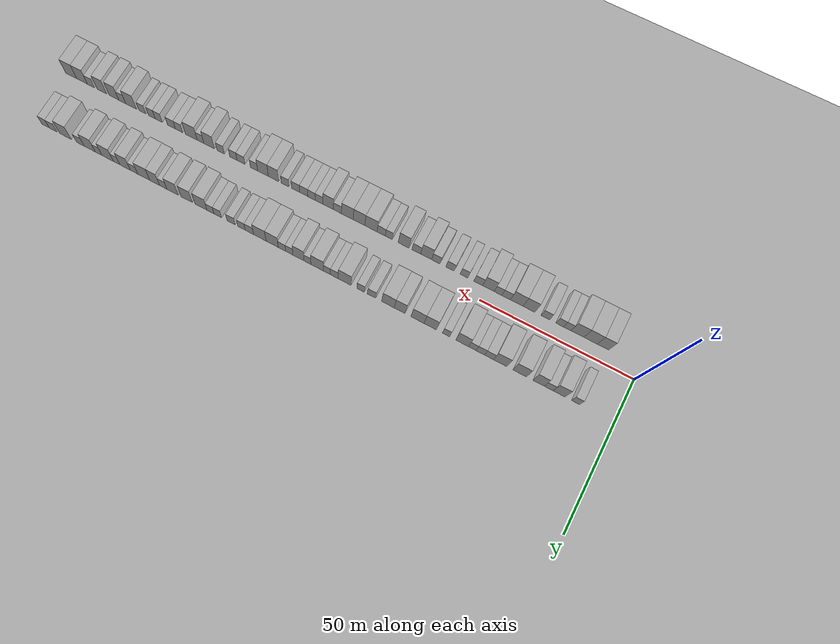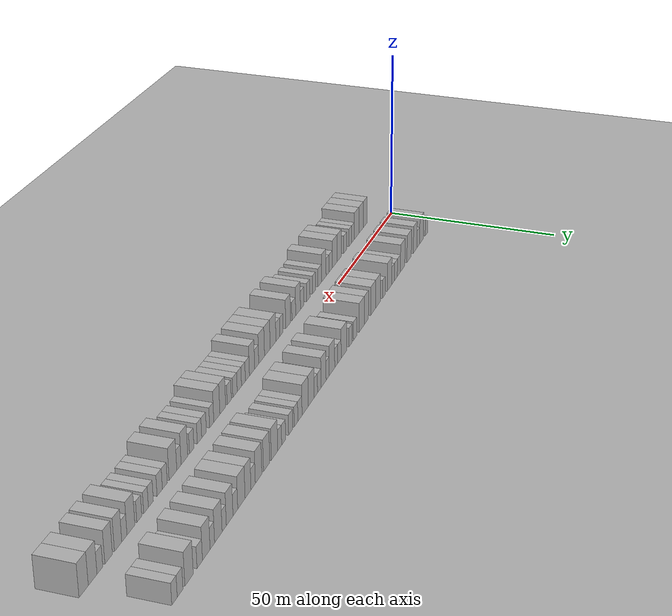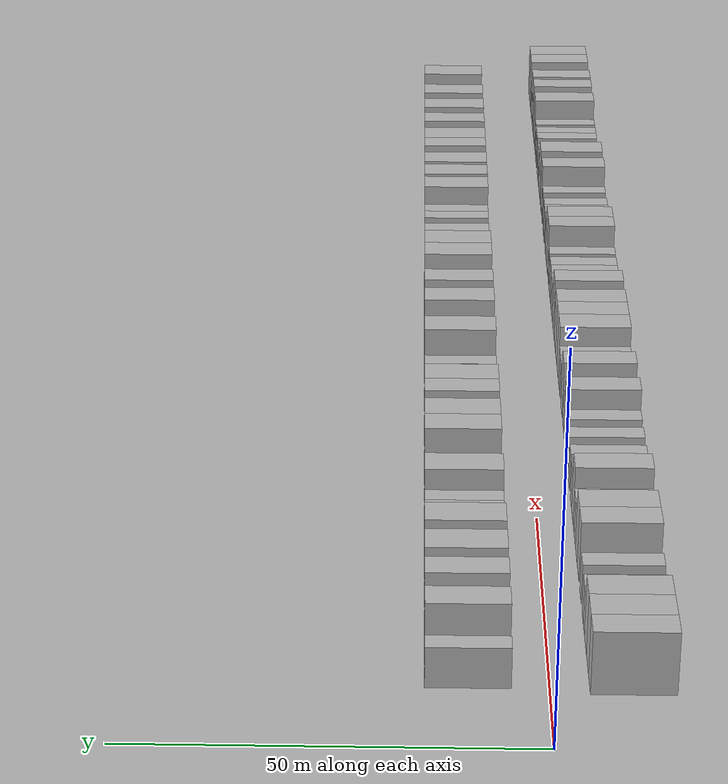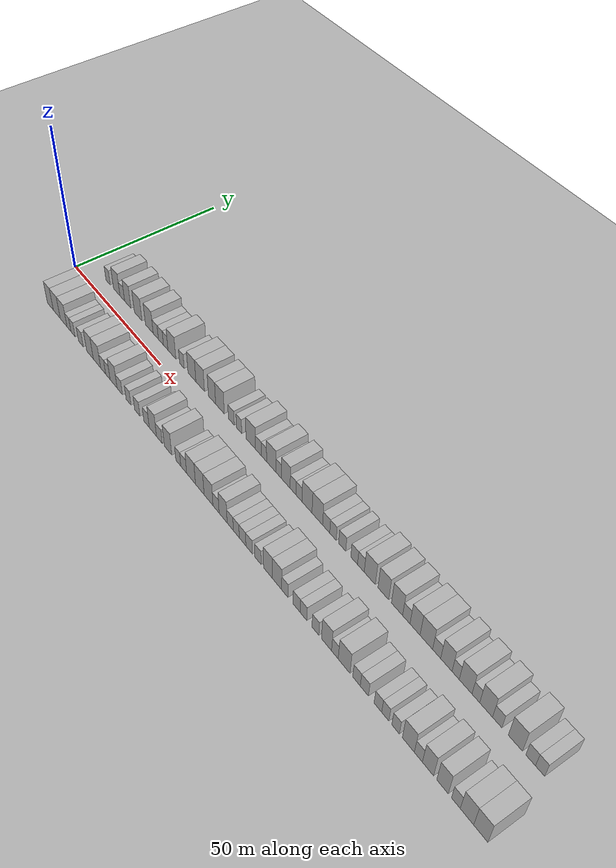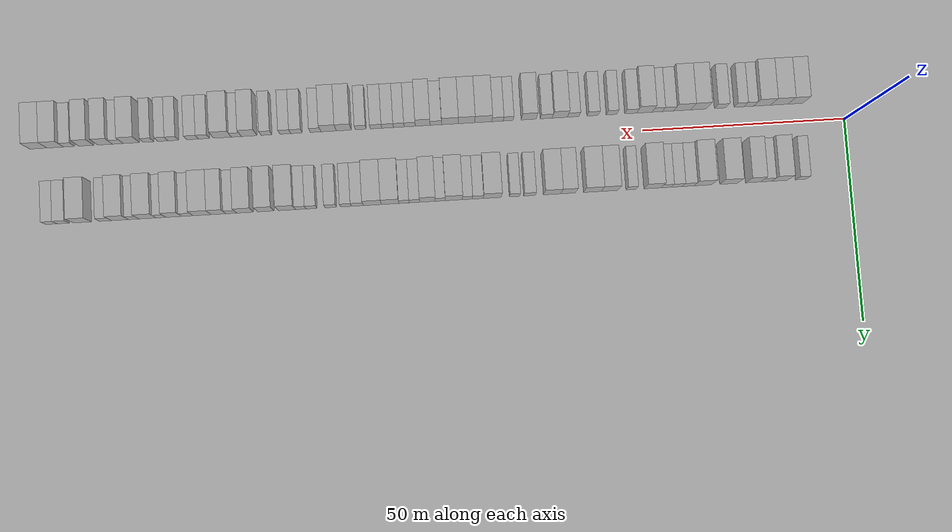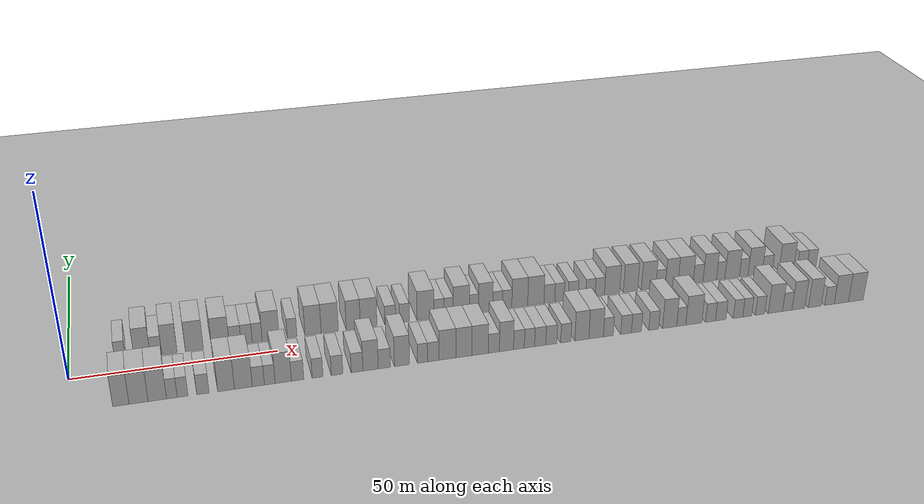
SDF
<?xml version="1.0" encoding="utf-8"?>

<sdf version="1.6">

   <world name="default">

      <gui fullscreen="0">

         <camera name="user_camera">

            <pose>-15 0 4.57585 0 0 0</pose>

            <view_controller>orbit</view_controller>

         </camera>

      </gui>

      <scene>

         <sky>

           <clouds>

             <speed>12</speed>

           </clouds>

         </sky>

         <ambient>0.4 0.4 0.4 1</ambient>

         <background>0.7 0.7 0.7 1</background>

         <shadows>1</shadows>

      </scene>

      <gravity>0 0 -9.8066</gravity>

      <magnetic_field>6e-06 2.3e-05 -4.2e-05</magnetic_field>

      <physics default="0" name="default_physics" type="ode">

         <ode>

            <solver>

               <type>quick</type>

               <iters>10</iters>

               <sor>1.0</sor>

               <use_dynamic_moi_rescaling>0</use_dynamic_moi_rescaling>

            </solver>

            <constraints>

               <cfm>0</cfm>

               <erp>0.2</erp>

               <contact_max_correcting_vel>100</contact_max_correcting_vel>

               <contact_surface_layer>0.001</contact_surface_layer>

            </constraints>

         </ode>

         <max_step_size>0.004</max_step_size>

         <real_time_factor>1</real_time_factor>

         <real_time_update_rate>250</real_time_update_rate>

      </physics>

      <light name="sun" type="directional">

         <cast_shadows>1</cast_shadows>

         <pose>0 0 10 0 0 0</pose>

         <diffuse>0.8 0.8 0.8 1</diffuse>

         <specular>0.2 0.2 0.2 1</specular>

         <attenuation>

            <range>1000</range>

            <constant>0.9</constant>

            <linear>0.01</linear>

            <quadratic>0.001</quadratic>

         </attenuation>

         <direction>-0.5 0.1 -0.9</direction>

      </light>

      <include>

         <name>ground_plane_1</name>

         <uri>model://HANNAS_ground_plane</uri>

         <pose>0 0 0  0 0 0</pose>

      </include>

      <include>

         <name>ground_plane_2</name>

         <uri>model://HANNAS_ground_plane</uri>

         <pose>100 0 0  0 0 0</pose>

      </include>

      <model name="building_1">

         <static>1</static>

         <pose frame="">12.2852 9.5000 0 0.000000 0.000000 1.570796</pose>

         <link name="link">

            <pose frame="">0 0 3.00 0 0 0</pose>

            <collision name="collision">

               <geometry>

                  <box>

                     <size>10.0000 2.5705 6.0000</size>

                  </box>

               </geometry>

               <max_contacts>10</max_contacts>

               <surface>

                  <contact>

                     <ode/>

                  </contact>

                  <bounce/>

                  <friction>

                     <torsional>

                        <ode/>

                     </torsional>

                     <ode/>

                  </friction>

               </surface>

            </collision>

            <visual name="visual">

               <cast_shadows>0</cast_shadows>

               <geometry>

                  <box>

                     <size>10.0000 2.5705 6.0000</size>

                  </box>

               </geometry>

               <material>

                  <script>

                     <uri>model://HANNAS_wall/materials/scripts</uri>

                     <uri>model://HANNAS_wall/materials/textures</uri>

                     <name>vrc/HANNAS_wall</name>

                  </script>

               </material>

            </visual>

            <self_collide>0</self_collide>

            <enable_wind>0</enable_wind>

            <kinematic>0</kinematic>

         </link>

      </model>

      <model name="building_2">

         <static>1</static>

         <pose frame="">17.4919 9.5000 0 0.000000 0.000000 1.570796</pose>

         <link name="link">

            <pose frame="">0 0 4.50 0 0 0</pose>

            <collision name="collision">

               <geometry>

                  <box>

                     <size>10.0000 3.8429 9.0000</size>

                  </box>

               </geometry>

               <max_contacts>10</max_contacts>

               <surface>

                  <contact>

                     <ode/>

                  </contact>

                  <bounce/>

                  <friction>

                     <torsional>

                        <ode/>

                     </torsional>

                     <ode/>

                  </friction>

               </surface>

            </collision>

            <visual name="visual">

               <cast_shadows>0</cast_shadows>

               <geometry>

                  <box>

                     <size>10.0000 3.8429 9.0000</size>

                  </box>

               </geometry>

               <material>

                  <script>

                     <uri>model://HANNAS_wall/materials/scripts</uri>

                     <uri>model://HANNAS_wall/materials/textures</uri>

                     <name>vrc/HANNAS_wall</name>

                  </script>

               </material>

            </visual>

            <self_collide>0</self_collide>

            <enable_wind>0</enable_wind>

            <kinematic>0</kinematic>

         </link>

      </model>

      <model name="building_3">

         <static>1</static>

         <pose frame="">20.8117 9.5000 0 0.000000 0.000000 1.570796</pose>

         <link name="link">

            <pose frame="">0 0 3.00 0 0 0</pose>

            <collision name="collision">

               <geometry>

                  <box>

                     <size>10.0000 2.7967 6.0000</size>

                  </box>

               </geometry>

               <max_contacts>10</max_contacts>

               <surface>

                  <contact>

                     <ode/>

                  </contact>

                  <bounce/>

                  <friction>

                     <torsional>

                        <ode/>

                     </torsional>

                     <ode/>

                  </friction>

               </surface>

            </collision>

            <visual name="visual">

               <cast_shadows>0</cast_shadows>

               <geometry>

                  <box>

                     <size>10.0000 2.7967 6.0000</size>

                  </box>

               </geometry>

               <material>

                  <script>

                     <uri>model://HANNAS_wall/materials/scripts</uri>

                     <uri>model://HANNAS_wall/materials/textures</uri>

                     <name>vrc/HANNAS_wall</name>

                  </script>

               </material>

            </visual>

            <self_collide>0</self_collide>

            <enable_wind>0</enable_wind>

            <kinematic>0</kinematic>

         </link>

      </model>

      <model name="building_4">

         <static>1</static>

         <pose frame="">24.0512 9.5000 0 0.000000 0.000000 1.570796</pose>

         <link name="link">

            <pose frame="">0 0 4.50 0 0 0</pose>

            <collision name="collision">

               <geometry>

                  <box>

                     <size>10.0000 3.6823 9.0000</size>

                  </box>

               </geometry>

               <max_contacts>10</max_contacts>

               <surface>

                  <contact>

                     <ode/>

                  </contact>

                  <bounce/>

                  <friction>

                     <torsional>

                        <ode/>

                     </torsional>

                     <ode/>

                  </friction>

               </surface>

            </collision>

            <visual name="visual">

               <cast_shadows>0</cast_shadows>

               <geometry>

                  <box>

                     <size>10.0000 3.6823 9.0000</size>

                  </box>

               </geometry>

               <material>

                  <script>

                     <uri>model://HANNAS_wall/materials/scripts</uri>

                     <uri>model://HANNAS_wall/materials/textures</uri>

                     <name>vrc/HANNAS_wall</name>

                  </script>

               </material>

            </visual>

            <self_collide>0</self_collide>

            <enable_wind>0</enable_wind>

            <kinematic>0</kinematic>

         </link>

      </model>

      <model name="building_5">

         <static>1</static>

         <pose frame="">30.0848 9.5000 0 0.000000 0.000000 1.570796</pose>

         <link name="link">

            <pose frame="">0 0 4.50 0 0 0</pose>

            <collision name="collision">

               <geometry>

                  <box>

                     <size>10.0000 4.3848 9.0000</size>

                  </box>

               </geometry>

               <max_contacts>10</max_contacts>

               <surface>

                  <contact>

                     <ode/>

                  </contact>

                  <bounce/>

                  <friction>

                     <torsional>

                        <ode/>

                     </torsional>

                     <ode/>

                  </friction>

               </surface>

            </collision>

            <visual name="visual">

               <cast_shadows>0</cast_shadows>

               <geometry>

                  <box>

                     <size>10.0000 4.3848 9.0000</size>

                  </box>

               </geometry>

               <material>

                  <script>

                     <uri>model://HANNAS_wall/materials/scripts</uri>

                     <uri>model://HANNAS_wall/materials/textures</uri>

                     <name>vrc/HANNAS_wall</name>

                  </script>

               </material>

            </visual>

            <self_collide>0</self_collide>

            <enable_wind>0</enable_wind>

            <kinematic>0</kinematic>

         </link>

      </model>

      <model name="building_6">

         <static>1</static>

         <pose frame="">36.4384 9.5000 0 0.000000 0.000000 1.570796</pose>

         <link name="link">

            <pose frame="">0 0 4.50 0 0 0</pose>

            <collision name="collision">

               <geometry>

                  <box>

                     <size>10.0000 4.3224 9.0000</size>

                  </box>

               </geometry>

               <max_contacts>10</max_contacts>

               <surface>

                  <contact>

                     <ode/>

                  </contact>

                  <bounce/>

                  <friction>

                     <torsional>

                        <ode/>

                     </torsional>

                     <ode/>

                  </friction>

               </surface>

            </collision>

            <visual name="visual">

               <cast_shadows>0</cast_shadows>

               <geometry>

                  <box>

                     <size>10.0000 4.3224 9.0000</size>

                  </box>

               </geometry>

               <material>

                  <script>

                     <uri>model://HANNAS_wall/materials/scripts</uri>

                     <uri>model://HANNAS_wall/materials/textures</uri>

                     <name>vrc/HANNAS_wall</name>

                  </script>

               </material>

            </visual>

            <self_collide>0</self_collide>

            <enable_wind>0</enable_wind>

            <kinematic>0</kinematic>

         </link>

      </model>

      <model name="building_7">

         <static>1</static>

         <pose frame="">40.0626 9.5000 0 0.000000 0.000000 1.570796</pose>

         <link name="link">

            <pose frame="">0 0 3.00 0 0 0</pose>

            <collision name="collision">

               <geometry>

                  <box>

                     <size>10.0000 2.9260 6.0000</size>

                  </box>

               </geometry>

               <max_contacts>10</max_contacts>

               <surface>

                  <contact>

                     <ode/>

                  </contact>

                  <bounce/>

                  <friction>

                     <torsional>

                        <ode/>

                     </torsional>

                     <ode/>

                  </friction>

               </surface>

            </collision>

            <visual name="visual">

               <cast_shadows>0</cast_shadows>

               <geometry>

                  <box>

                     <size>10.0000 2.9260 6.0000</size>

                  </box>

               </geometry>

               <material>

                  <script>

                     <uri>model://HANNAS_wall/materials/scripts</uri>

                     <uri>model://HANNAS_wall/materials/textures</uri>

                     <name>vrc/HANNAS_wall</name>

                  </script>

               </material>

            </visual>

            <self_collide>0</self_collide>

            <enable_wind>0</enable_wind>

            <kinematic>0</kinematic>

         </link>

      </model>

      <model name="building_8">

         <static>1</static>

         <pose frame="">42.9022 9.5000 0 0.000000 0.000000 1.570796</pose>

         <link name="link">

            <pose frame="">0 0 3.00 0 0 0</pose>

            <collision name="collision">

               <geometry>

                  <box>

                     <size>10.0000 2.7533 6.0000</size>

                  </box>

               </geometry>

               <max_contacts>10</max_contacts>

               <surface>

                  <contact>

                     <ode/>

                  </contact>

                  <bounce/>

                  <friction>

                     <torsional>

                        <ode/>

                     </torsional>

                     <ode/>

                  </friction>

               </surface>

            </collision>

            <visual name="visual">

               <cast_shadows>0</cast_shadows>

               <geometry>

                  <box>

                     <size>10.0000 2.7533 6.0000</size>

                  </box>

               </geometry>

               <material>

                  <script>

                     <uri>model://HANNAS_wall/materials/scripts</uri>

                     <uri>model://HANNAS_wall/materials/textures</uri>

                     <name>vrc/HANNAS_wall</name>

                  </script>

               </material>

            </visual>

            <self_collide>0</self_collide>

            <enable_wind>0</enable_wind>

            <kinematic>0</kinematic>

         </link>

      </model>

      <model name="building_9">

         <static>1</static>

         <pose frame="">45.5193 9.5000 0 0.000000 0.000000 1.570796</pose>

         <link name="link">

            <pose frame="">0 0 3.00 0 0 0</pose>

            <collision name="collision">

               <geometry>

                  <box>

                     <size>10.0000 2.4808 6.0000</size>

                  </box>

               </geometry>

               <max_contacts>10</max_contacts>

               <surface>

                  <contact>

                     <ode/>

                  </contact>

                  <bounce/>

                  <friction>

                     <torsional>

                        <ode/>

                     </torsional>

                     <ode/>

                  </friction>

               </surface>

            </collision>

            <visual name="visual">

               <cast_shadows>0</cast_shadows>

               <geometry>

                  <box>

                     <size>10.0000 2.4808 6.0000</size>

                  </box>

               </geometry>

               <material>

                  <script>

                     <uri>model://HANNAS_wall/materials/scripts</uri>

                     <uri>model://HANNAS_wall/materials/textures</uri>

                     <name>vrc/HANNAS_wall</name>

                  </script>

               </material>

            </visual>

            <self_collide>0</self_collide>

            <enable_wind>0</enable_wind>

            <kinematic>0</kinematic>

         </link>

      </model>

      <model name="building_10">

         <static>1</static>

         <pose frame="">48.8832 9.5000 0 0.000000 0.000000 1.570796</pose>

         <link name="link">

            <pose frame="">0 0 4.50 0 0 0</pose>

            <collision name="collision">

               <geometry>

                  <box>

                     <size>10.0000 4.2470 9.0000</size>

                  </box>

               </geometry>

               <max_contacts>10</max_contacts>

               <surface>

                  <contact>

                     <ode/>

                  </contact>

                  <bounce/>

                  <friction>

                     <torsional>

                        <ode/>

                     </torsional>

                     <ode/>

                  </friction>

               </surface>

            </collision>

            <visual name="visual">

               <cast_shadows>0</cast_shadows>

               <geometry>

                  <box>

                     <size>10.0000 4.2470 9.0000</size>

                  </box>

               </geometry>

               <material>

                  <script>

                     <uri>model://HANNAS_wall/materials/scripts</uri>

                     <uri>model://HANNAS_wall/materials/textures</uri>

                     <name>vrc/HANNAS_wall</name>

                  </script>

               </material>

            </visual>

            <self_collide>0</self_collide>

            <enable_wind>0</enable_wind>

            <kinematic>0</kinematic>

         </link>

      </model>

      <model name="building_11">

         <static>1</static>

         <pose frame="">54.2244 9.5000 0 0.000000 0.000000 1.570796</pose>

         <link name="link">

            <pose frame="">0 0 3.00 0 0 0</pose>

            <collision name="collision">

               <geometry>

                  <box>

                     <size>10.0000 2.4354 6.0000</size>

                  </box>

               </geometry>

               <max_contacts>10</max_contacts>

               <surface>

                  <contact>

                     <ode/>

                  </contact>

                  <bounce/>

                  <friction>

                     <torsional>

                        <ode/>

                     </torsional>

                     <ode/>

                  </friction>

               </surface>

            </collision>

            <visual name="visual">

               <cast_shadows>0</cast_shadows>

               <geometry>

                  <box>

                     <size>10.0000 2.4354 6.0000</size>

                  </box>

               </geometry>

               <material>

                  <script>

                     <uri>model://HANNAS_wall/materials/scripts</uri>

                     <uri>model://HANNAS_wall/materials/textures</uri>

                     <name>vrc/HANNAS_wall</name>

                  </script>

               </material>

            </visual>

            <self_collide>0</self_collide>

            <enable_wind>0</enable_wind>

            <kinematic>0</kinematic>

         </link>

      </model>

      <model name="building_12">

         <static>1</static>

         <pose frame="">59.4938 9.5000 0 0.000000 0.000000 1.570796</pose>

         <link name="link">

            <pose frame="">0 0 4.50 0 0 0</pose>

            <collision name="collision">

               <geometry>

                  <box>

                     <size>10.0000 4.1035 9.0000</size>

                  </box>

               </geometry>

               <max_contacts>10</max_contacts>

               <surface>

                  <contact>

                     <ode/>

                  </contact>

                  <bounce/>

                  <friction>

                     <torsional>

                        <ode/>

                     </torsional>

                     <ode/>

                  </friction>

               </surface>

            </collision>

            <visual name="visual">

               <cast_shadows>0</cast_shadows>

               <geometry>

                  <box>

                     <size>10.0000 4.1035 9.0000</size>

                  </box>

               </geometry>

               <material>

                  <script>

                     <uri>model://HANNAS_wall/materials/scripts</uri>

                     <uri>model://HANNAS_wall/materials/textures</uri>

                     <name>vrc/HANNAS_wall</name>

                  </script>

               </material>

            </visual>

            <self_collide>0</self_collide>

            <enable_wind>0</enable_wind>

            <kinematic>0</kinematic>

         </link>

      </model>

      <model name="building_13">

         <static>1</static>

         <pose frame="">63.7356 9.5000 0 0.000000 0.000000 1.570796</pose>

         <link name="link">

            <pose frame="">0 0 4.50 0 0 0</pose>

            <collision name="collision">

               <geometry>

                  <box>

                     <size>10.0000 4.3802 9.0000</size>

                  </box>

               </geometry>

               <max_contacts>10</max_contacts>

               <surface>

                  <contact>

                     <ode/>

                  </contact>

                  <bounce/>

                  <friction>

                     <torsional>

                        <ode/>

                     </torsional>

                     <ode/>

                  </friction>

               </surface>

            </collision>

            <visual name="visual">

               <cast_shadows>0</cast_shadows>

               <geometry>

                  <box>

                     <size>10.0000 4.3802 9.0000</size>

                  </box>

               </geometry>

               <material>

                  <script>

                     <uri>model://HANNAS_wall/materials/scripts</uri>

                     <uri>model://HANNAS_wall/materials/textures</uri>

                     <name>vrc/HANNAS_wall</name>

                  </script>

               </material>

            </visual>

            <self_collide>0</self_collide>

            <enable_wind>0</enable_wind>

            <kinematic>0</kinematic>

         </link>

      </model>

      <model name="building_14">

         <static>1</static>

         <pose frame="">69.7383 9.5000 0 0.000000 0.000000 1.570796</pose>

         <link name="link">

            <pose frame="">0 0 4.50 0 0 0</pose>

            <collision name="collision">

               <geometry>

                  <box>

                     <size>10.0000 3.6252 9.0000</size>

                  </box>

               </geometry>

               <max_contacts>10</max_contacts>

               <surface>

                  <contact>

                     <ode/>

                  </contact>

                  <bounce/>

                  <friction>

                     <torsional>

                        <ode/>

                     </torsional>

                     <ode/>

                  </friction>

               </surface>

            </collision>

            <visual name="visual">

               <cast_shadows>0</cast_shadows>

               <geometry>

                  <box>

                     <size>10.0000 3.6252 9.0000</size>

                  </box>

               </geometry>

               <material>

                  <script>

                     <uri>model://HANNAS_wall/materials/scripts</uri>

                     <uri>model://HANNAS_wall/materials/textures</uri>

                     <name>vrc/HANNAS_wall</name>

                  </script>

               </material>

            </visual>

            <self_collide>0</self_collide>

            <enable_wind>0</enable_wind>

            <kinematic>0</kinematic>

         </link>

      </model>

      <model name="building_15">

         <static>1</static>

         <pose frame="">73.6824 9.5000 0 0.000000 0.000000 1.570796</pose>

         <link name="link">

            <pose frame="">0 0 4.50 0 0 0</pose>

            <collision name="collision">

               <geometry>

                  <box>

                     <size>10.0000 4.2629 9.0000</size>

                  </box>

               </geometry>

               <max_contacts>10</max_contacts>

               <surface>

                  <contact>

                     <ode/>

                  </contact>

                  <bounce/>

                  <friction>

                     <torsional>

                        <ode/>

                     </torsional>

                     <ode/>

                  </friction>

               </surface>

            </collision>

            <visual name="visual">

               <cast_shadows>0</cast_shadows>

               <geometry>

                  <box>

                     <size>10.0000 4.2629 9.0000</size>

                  </box>

               </geometry>

               <material>

                  <script>

                     <uri>model://HANNAS_wall/materials/scripts</uri>

                     <uri>model://HANNAS_wall/materials/textures</uri>

                     <name>vrc/HANNAS_wall</name>

                  </script>

               </material>

            </visual>

            <self_collide>0</self_collide>

            <enable_wind>0</enable_wind>

            <kinematic>0</kinematic>

         </link>

      </model>

      <model name="building_16">

         <static>1</static>

         <pose frame="">79.2487 9.5000 0 0.000000 0.000000 1.570796</pose>

         <link name="link">

            <pose frame="">0 0 3.00 0 0 0</pose>

            <collision name="collision">

               <geometry>

                  <box>

                     <size>10.0000 2.8696 6.0000</size>

                  </box>

               </geometry>

               <max_contacts>10</max_contacts>

               <surface>

                  <contact>

                     <ode/>

                  </contact>

                  <bounce/>

                  <friction>

                     <torsional>

                        <ode/>

                     </torsional>

                     <ode/>

                  </friction>

               </surface>

            </collision>

            <visual name="visual">

               <cast_shadows>0</cast_shadows>

               <geometry>

                  <box>

                     <size>10.0000 2.8696 6.0000</size>

                  </box>

               </geometry>

               <material>

                  <script>

                     <uri>model://HANNAS_wall/materials/scripts</uri>

                     <uri>model://HANNAS_wall/materials/textures</uri>

                     <name>vrc/HANNAS_wall</name>

                  </script>

               </material>

            </visual>

            <self_collide>0</self_collide>

            <enable_wind>0</enable_wind>

            <kinematic>0</kinematic>

         </link>

      </model>

      <model name="building_17">

         <static>1</static>

         <pose frame="">82.9593 9.5000 0 0.000000 0.000000 1.570796</pose>

         <link name="link">

            <pose frame="">0 0 3.00 0 0 0</pose>

            <collision name="collision">

               <geometry>

                  <box>

                     <size>10.0000 2.5515 6.0000</size>

                  </box>

               </geometry>

               <max_contacts>10</max_contacts>

               <surface>

                  <contact>

                     <ode/>

                  </contact>

                  <bounce/>

                  <friction>

                     <torsional>

                        <ode/>

                     </torsional>

                     <ode/>

                  </friction>

               </surface>

            </collision>

            <visual name="visual">

               <cast_shadows>0</cast_shadows>

               <geometry>

                  <box>

                     <size>10.0000 2.5515 6.0000</size>

                  </box>

               </geometry>

               <material>

                  <script>

                     <uri>model://HANNAS_wall/materials/scripts</uri>

                     <uri>model://HANNAS_wall/materials/textures</uri>

                     <name>vrc/HANNAS_wall</name>

                  </script>

               </material>

            </visual>

            <self_collide>0</self_collide>

            <enable_wind>0</enable_wind>

            <kinematic>0</kinematic>

         </link>

      </model>

      <model name="building_18">

         <static>1</static>

         <pose frame="">88.4551 9.5000 0 0.000000 0.000000 1.570796</pose>

         <link name="link">

            <pose frame="">0 0 4.50 0 0 0</pose>

            <collision name="collision">

               <geometry>

                  <box>

                     <size>10.0000 4.4401 9.0000</size>

                  </box>

               </geometry>

               <max_contacts>10</max_contacts>

               <surface>

                  <contact>

                     <ode/>

                  </contact>

                  <bounce/>

                  <friction>

                     <torsional>

                        <ode/>

                     </torsional>

                     <ode/>

                  </friction>

               </surface>

            </collision>

            <visual name="visual">

               <cast_shadows>0</cast_shadows>

               <geometry>

                  <box>

                     <size>10.0000 4.4401 9.0000</size>

                  </box>

               </geometry>

               <material>

                  <script>

                     <uri>model://HANNAS_wall/materials/scripts</uri>

                     <uri>model://HANNAS_wall/materials/textures</uri>

                     <name>vrc/HANNAS_wall</name>

                  </script>

               </material>

            </visual>

            <self_collide>0</self_collide>

            <enable_wind>0</enable_wind>

            <kinematic>0</kinematic>

         </link>

      </model>

      <model name="building_19">

         <static>1</static>

         <pose frame="">92.0016 9.5000 0 0.000000 0.000000 1.570796</pose>

         <link name="link">

            <pose frame="">0 0 3.00 0 0 0</pose>

            <collision name="collision">

               <geometry>

                  <box>

                     <size>10.0000 2.6529 6.0000</size>

                  </box>

               </geometry>

               <max_contacts>10</max_contacts>

               <surface>

                  <contact>

                     <ode/>

                  </contact>

                  <bounce/>

                  <friction>

                     <torsional>

                        <ode/>

                     </torsional>

                     <ode/>

                  </friction>

               </surface>

            </collision>

            <visual name="visual">

               <cast_shadows>0</cast_shadows>

               <geometry>

                  <box>

                     <size>10.0000 2.6529 6.0000</size>

                  </box>

               </geometry>

               <material>

                  <script>

                     <uri>model://HANNAS_wall/materials/scripts</uri>

                     <uri>model://HANNAS_wall/materials/textures</uri>

                     <name>vrc/HANNAS_wall</name>

                  </script>

               </material>

            </visual>

            <self_collide>0</self_collide>

            <enable_wind>0</enable_wind>

            <kinematic>0</kinematic>

         </link>

      </model>

      <model name="building_20">

         <static>1</static>

         <pose frame="">94.5586 9.5000 0 0.000000 0.000000 1.570796</pose>

         <link name="link">

            <pose frame="">0 0 3.00 0 0 0</pose>

            <collision name="collision">

               <geometry>

                  <box>

                     <size>10.0000 2.4611 6.0000</size>

                  </box>

               </geometry>

               <max_contacts>10</max_contacts>

               <surface>

                  <contact>

                     <ode/>

                  </contact>

                  <bounce/>

                  <friction>

                     <torsional>

                        <ode/>

                     </torsional>

                     <ode/>

                  </friction>

               </surface>

            </collision>

            <visual name="visual">

               <cast_shadows>0</cast_shadows>

               <geometry>

                  <box>

                     <size>10.0000 2.4611 6.0000</size>

                  </box>

               </geometry>

               <material>

                  <script>

                     <uri>model://HANNAS_wall/materials/scripts</uri>

                     <uri>model://HANNAS_wall/materials/textures</uri>

                     <name>vrc/HANNAS_wall</name>

                  </script>

               </material>

            </visual>

            <self_collide>0</self_collide>

            <enable_wind>0</enable_wind>

            <kinematic>0</kinematic>

         </link>

      </model>

      <model name="building_21">

         <static>1</static>

         <pose frame="">97.9158 9.5000 0 0.000000 0.000000 1.570796</pose>

         <link name="link">

            <pose frame="">0 0 4.50 0 0 0</pose>

            <collision name="collision">

               <geometry>

                  <box>

                     <size>10.0000 4.2533 9.0000</size>

                  </box>

               </geometry>

               <max_contacts>10</max_contacts>

               <surface>

                  <contact>

                     <ode/>

                  </contact>

                  <bounce/>

                  <friction>

                     <torsional>

                        <ode/>

                     </torsional>

                     <ode/>

                  </friction>

               </surface>

            </collision>

            <visual name="visual">

               <cast_shadows>0</cast_shadows>

               <geometry>

                  <box>

                     <size>10.0000 4.2533 9.0000</size>

                  </box>

               </geometry>

               <material>

                  <script>

                     <uri>model://HANNAS_wall/materials/scripts</uri>

                     <uri>model://HANNAS_wall/materials/textures</uri>

                     <name>vrc/HANNAS_wall</name>

                  </script>

               </material>

            </visual>

            <self_collide>0</self_collide>

            <enable_wind>0</enable_wind>

            <kinematic>0</kinematic>

         </link>

      </model>

      <model name="building_22">

         <static>1</static>

         <pose frame="">101.2465 9.5000 0 0.000000 0.000000 1.570796</pose>

         <link name="link">

            <pose frame="">0 0 3.00 0 0 0</pose>

            <collision name="collision">

               <geometry>

                  <box>

                     <size>10.0000 2.4080 6.0000</size>

                  </box>

               </geometry>

               <max_contacts>10</max_contacts>

               <surface>

                  <contact>

                     <ode/>

                  </contact>

                  <bounce/>

                  <friction>

                     <torsional>

                        <ode/>

                     </torsional>

                     <ode/>

                  </friction>

               </surface>

            </collision>

            <visual name="visual">

               <cast_shadows>0</cast_shadows>

               <geometry>

                  <box>

                     <size>10.0000 2.4080 6.0000</size>

                  </box>

               </geometry>

               <material>

                  <script>

                     <uri>model://HANNAS_wall/materials/scripts</uri>

                     <uri>model://HANNAS_wall/materials/textures</uri>

                     <name>vrc/HANNAS_wall</name>

                  </script>

               </material>

            </visual>

            <self_collide>0</self_collide>

            <enable_wind>0</enable_wind>

            <kinematic>0</kinematic>

         </link>

      </model>

      <model name="building_23">

         <static>1</static>

         <pose frame="">104.3787 9.5000 0 0.000000 0.000000 1.570796</pose>

         <link name="link">

            <pose frame="">0 0 4.50 0 0 0</pose>

            <collision name="collision">

               <geometry>

                  <box>

                     <size>10.0000 3.8563 9.0000</size>

                  </box>

               </geometry>

               <max_contacts>10</max_contacts>

               <surface>

                  <contact>

                     <ode/>

                  </contact>

                  <bounce/>

                  <friction>

                     <torsional>

                        <ode/>

                     </torsional>

                     <ode/>

                  </friction>

               </surface>

            </collision>

            <visual name="visual">

               <cast_shadows>0</cast_shadows>

               <geometry>

                  <box>

                     <size>10.0000 3.8563 9.0000</size>

                  </box>

               </geometry>

               <material>

                  <script>

                     <uri>model://HANNAS_wall/materials/scripts</uri>

                     <uri>model://HANNAS_wall/materials/textures</uri>

                     <name>vrc/HANNAS_wall</name>

                  </script>

               </material>

            </visual>

            <self_collide>0</self_collide>

            <enable_wind>0</enable_wind>

            <kinematic>0</kinematic>

         </link>

      </model>

      <model name="building_24">

         <static>1</static>

         <pose frame="">107.5938 9.5000 0 0.000000 0.000000 1.570796</pose>

         <link name="link">

            <pose frame="">0 0 3.00 0 0 0</pose>

            <collision name="collision">

               <geometry>

                  <box>

                     <size>10.0000 2.5739 6.0000</size>

                  </box>

               </geometry>

               <max_contacts>10</max_contacts>

               <surface>

                  <contact>

                     <ode/>

                  </contact>

                  <bounce/>

                  <friction>

                     <torsional>

                        <ode/>

                     </torsional>

                     <ode/>

                  </friction>

               </surface>

            </collision>

            <visual name="visual">

               <cast_shadows>0</cast_shadows>

               <geometry>

                  <box>

                     <size>10.0000 2.5739 6.0000</size>

                  </box>

               </geometry>

               <material>

                  <script>

                     <uri>model://HANNAS_wall/materials/scripts</uri>

                     <uri>model://HANNAS_wall/materials/textures</uri>

                     <name>vrc/HANNAS_wall</name>

                  </script>

               </material>

            </visual>

            <self_collide>0</self_collide>

            <enable_wind>0</enable_wind>

            <kinematic>0</kinematic>

         </link>

      </model>

      <model name="building_25">

         <static>1</static>

         <pose frame="">110.1495 9.5000 0 0.000000 0.000000 1.570796</pose>

         <link name="link">

            <pose frame="">0 0 3.00 0 0 0</pose>

            <collision name="collision">

               <geometry>

                  <box>

                     <size>10.0000 2.5376 6.0000</size>

                  </box>

               </geometry>

               <max_contacts>10</max_contacts>

               <surface>

                  <contact>

                     <ode/>

                  </contact>

                  <bounce/>

                  <friction>

                     <torsional>

                        <ode/>

                     </torsional>

                     <ode/>

                  </friction>

               </surface>

            </collision>

            <visual name="visual">

               <cast_shadows>0</cast_shadows>

               <geometry>

                  <box>

                     <size>10.0000 2.5376 6.0000</size>

                  </box>

               </geometry>

               <material>

                  <script>

                     <uri>model://HANNAS_wall/materials/scripts</uri>

                     <uri>model://HANNAS_wall/materials/textures</uri>

                     <name>vrc/HANNAS_wall</name>

                  </script>

               </material>

            </visual>

            <self_collide>0</self_collide>

            <enable_wind>0</enable_wind>

            <kinematic>0</kinematic>

         </link>

      </model>

      <model name="building_26">

         <static>1</static>

         <pose frame="">113.5669 9.5000 0 0.000000 0.000000 1.570796</pose>

         <link name="link">

            <pose frame="">0 0 4.50 0 0 0</pose>

            <collision name="collision">

               <geometry>

                  <box>

                     <size>10.0000 4.2973 9.0000</size>

                  </box>

               </geometry>

               <max_contacts>10</max_contacts>

               <surface>

                  <contact>

                     <ode/>

                  </contact>

                  <bounce/>

                  <friction>

                     <torsional>

                        <ode/>

                     </torsional>

                     <ode/>

                  </friction>

               </surface>

            </collision>

            <visual name="visual">

               <cast_shadows>0</cast_shadows>

               <geometry>

                  <box>

                     <size>10.0000 4.2973 9.0000</size>

                  </box>

               </geometry>

               <material>

                  <script>

                     <uri>model://HANNAS_wall/materials/scripts</uri>

                     <uri>model://HANNAS_wall/materials/textures</uri>

                     <name>vrc/HANNAS_wall</name>

                  </script>

               </material>

            </visual>

            <self_collide>0</self_collide>

            <enable_wind>0</enable_wind>

            <kinematic>0</kinematic>

         </link>

      </model>

      <model name="building_27">

         <static>1</static>

         <pose frame="">117.9323 9.5000 0 0.000000 0.000000 1.570796</pose>

         <link name="link">

            <pose frame="">0 0 4.50 0 0 0</pose>

            <collision name="collision">

               <geometry>

                  <box>

                     <size>10.0000 4.4335 9.0000</size>

                  </box>

               </geometry>

               <max_contacts>10</max_contacts>

               <surface>

                  <contact>

                     <ode/>

                  </contact>

                  <bounce/>

                  <friction>

                     <torsional>

                        <ode/>

                     </torsional>

                     <ode/>

                  </friction>

               </surface>

            </collision>

            <visual name="visual">

               <cast_shadows>0</cast_shadows>

               <geometry>

                  <box>

                     <size>10.0000 4.4335 9.0000</size>

                  </box>

               </geometry>

               <material>

                  <script>

                     <uri>model://HANNAS_wall/materials/scripts</uri>

                     <uri>model://HANNAS_wall/materials/textures</uri>

                     <name>vrc/HANNAS_wall</name>

                  </script>

               </material>

            </visual>

            <self_collide>0</self_collide>

            <enable_wind>0</enable_wind>

            <kinematic>0</kinematic>

         </link>

      </model>

      <model name="building_28">

         <static>1</static>

         <pose frame="">121.6269 9.5000 0 0.000000 0.000000 1.570796</pose>

         <link name="link">

            <pose frame="">0 0 3.00 0 0 0</pose>

            <collision name="collision">

               <geometry>

                  <box>

                     <size>10.0000 2.9556 6.0000</size>

                  </box>

               </geometry>

               <max_contacts>10</max_contacts>

               <surface>

                  <contact>

                     <ode/>

                  </contact>

                  <bounce/>

                  <friction>

                     <torsional>

                        <ode/>

                     </torsional>

                     <ode/>

                  </friction>

               </surface>

            </collision>

            <visual name="visual">

               <cast_shadows>0</cast_shadows>

               <geometry>

                  <box>

                     <size>10.0000 2.9556 6.0000</size>

                  </box>

               </geometry>

               <material>

                  <script>

                     <uri>model://HANNAS_wall/materials/scripts</uri>

                     <uri>model://HANNAS_wall/materials/textures</uri>

                     <name>vrc/HANNAS_wall</name>

                  </script>

               </material>

            </visual>

            <self_collide>0</self_collide>

            <enable_wind>0</enable_wind>

            <kinematic>0</kinematic>

         </link>

      </model>

      <model name="building_29">

         <static>1</static>

         <pose frame="">124.4166 9.5000 0 0.000000 0.000000 1.570796</pose>

         <link name="link">

            <pose frame="">0 0 3.00 0 0 0</pose>

            <collision name="collision">

               <geometry>

                  <box>

                     <size>10.0000 2.6238 6.0000</size>

                  </box>

               </geometry>

               <max_contacts>10</max_contacts>

               <surface>

                  <contact>

                     <ode/>

                  </contact>

                  <bounce/>

                  <friction>

                     <torsional>

                        <ode/>

                     </torsional>

                     <ode/>

                  </friction>

               </surface>

            </collision>

            <visual name="visual">

               <cast_shadows>0</cast_shadows>

               <geometry>

                  <box>

                     <size>10.0000 2.6238 6.0000</size>

                  </box>

               </geometry>

               <material>

                  <script>

                     <uri>model://HANNAS_wall/materials/scripts</uri>

                     <uri>model://HANNAS_wall/materials/textures</uri>

                     <name>vrc/HANNAS_wall</name>

                  </script>

               </material>

            </visual>

            <self_collide>0</self_collide>

            <enable_wind>0</enable_wind>

            <kinematic>0</kinematic>

         </link>

      </model>

      <model name="building_30">

         <static>1</static>

         <pose frame="">128.1461 9.5000 0 0.000000 0.000000 1.570796</pose>

         <link name="link">

            <pose frame="">0 0 3.00 0 0 0</pose>

            <collision name="collision">

               <geometry>

                  <box>

                     <size>10.0000 2.8352 6.0000</size>

                  </box>

               </geometry>

               <max_contacts>10</max_contacts>

               <surface>

                  <contact>

                     <ode/>

                  </contact>

                  <bounce/>

                  <friction>

                     <torsional>

                        <ode/>

                     </torsional>

                     <ode/>

                  </friction>

               </surface>

            </collision>

            <visual name="visual">

               <cast_shadows>0</cast_shadows>

               <geometry>

                  <box>

                     <size>10.0000 2.8352 6.0000</size>

                  </box>

               </geometry>

               <material>

                  <script>

                     <uri>model://HANNAS_wall/materials/scripts</uri>

                     <uri>model://HANNAS_wall/materials/textures</uri>

                     <name>vrc/HANNAS_wall</name>

                  </script>

               </material>

            </visual>

            <self_collide>0</self_collide>

            <enable_wind>0</enable_wind>

            <kinematic>0</kinematic>

         </link>

      </model>

      <model name="building_31">

         <static>1</static>

         <pose frame="">132.9015 9.5000 0 0.000000 0.000000 1.570796</pose>

         <link name="link">

            <pose frame="">0 0 3.00 0 0 0</pose>

            <collision name="collision">

               <geometry>

                  <box>

                     <size>10.0000 2.6755 6.0000</size>

                  </box>

               </geometry>

               <max_contacts>10</max_contacts>

               <surface>

                  <contact>

                     <ode/>

                  </contact>

                  <bounce/>

                  <friction>

                     <torsional>

                        <ode/>

                     </torsional>

                     <ode/>

                  </friction>

               </surface>

            </collision>

            <visual name="visual">

               <cast_shadows>0</cast_shadows>

               <geometry>

                  <box>

                     <size>10.0000 2.6755 6.0000</size>

                  </box>

               </geometry>

               <material>

                  <script>

                     <uri>model://HANNAS_wall/materials/scripts</uri>

                     <uri>model://HANNAS_wall/materials/textures</uri>

                     <name>vrc/HANNAS_wall</name>

                  </script>

               </material>

            </visual>

            <self_collide>0</self_collide>

            <enable_wind>0</enable_wind>

            <kinematic>0</kinematic>

         </link>

      </model>

      <model name="building_32">

         <static>1</static>

         <pose frame="">135.5398 9.5000 0 0.000000 0.000000 1.570796</pose>

         <link name="link">

            <pose frame="">0 0 3.00 0 0 0</pose>

            <collision name="collision">

               <geometry>

                  <box>

                     <size>10.0000 2.6013 6.0000</size>

                  </box>

               </geometry>

               <max_contacts>10</max_contacts>

               <surface>

                  <contact>

                     <ode/>

                  </contact>

                  <bounce/>

                  <friction>

                     <torsional>

                        <ode/>

                     </torsional>

                     <ode/>

                  </friction>

               </surface>

            </collision>

            <visual name="visual">

               <cast_shadows>0</cast_shadows>

               <geometry>

                  <box>

                     <size>10.0000 2.6013 6.0000</size>

                  </box>

               </geometry>

               <material>

                  <script>

                     <uri>model://HANNAS_wall/materials/scripts</uri>

                     <uri>model://HANNAS_wall/materials/textures</uri>

                     <name>vrc/HANNAS_wall</name>

                  </script>

               </material>

            </visual>

            <self_collide>0</self_collide>

            <enable_wind>0</enable_wind>

            <kinematic>0</kinematic>

         </link>

      </model>

      <model name="building_33">

         <static>1</static>

         <pose frame="">138.9827 9.5000 0 0.000000 0.000000 1.570796</pose>

         <link name="link">

            <pose frame="">0 0 4.50 0 0 0</pose>

            <collision name="collision">

               <geometry>

                  <box>

                     <size>10.0000 4.2845 9.0000</size>

                  </box>

               </geometry>

               <max_contacts>10</max_contacts>

               <surface>

                  <contact>

                     <ode/>

                  </contact>

                  <bounce/>

                  <friction>

                     <torsional>

                        <ode/>

                     </torsional>

                     <ode/>

                  </friction>

               </surface>

            </collision>

            <visual name="visual">

               <cast_shadows>0</cast_shadows>

               <geometry>

                  <box>

                     <size>10.0000 4.2845 9.0000</size>

                  </box>

               </geometry>

               <material>

                  <script>

                     <uri>model://HANNAS_wall/materials/scripts</uri>

                     <uri>model://HANNAS_wall/materials/textures</uri>

                     <name>vrc/HANNAS_wall</name>

                  </script>

               </material>

            </visual>

            <self_collide>0</self_collide>

            <enable_wind>0</enable_wind>

            <kinematic>0</kinematic>

         </link>

      </model>

      <model name="building_34">

         <static>1</static>

         <pose frame="">144.1502 9.5000 0 0.000000 0.000000 1.570796</pose>

         <link name="link">

            <pose frame="">0 0 4.50 0 0 0</pose>

            <collision name="collision">

               <geometry>

                  <box>

                     <size>10.0000 4.0504 9.0000</size>

                  </box>

               </geometry>

               <max_contacts>10</max_contacts>

               <surface>

                  <contact>

                     <ode/>

                  </contact>

                  <bounce/>

                  <friction>

                     <torsional>

                        <ode/>

                     </torsional>

                     <ode/>

                  </friction>

               </surface>

            </collision>

            <visual name="visual">

               <cast_shadows>0</cast_shadows>

               <geometry>

                  <box>

                     <size>10.0000 4.0504 9.0000</size>

                  </box>

               </geometry>

               <material>

                  <script>

                     <uri>model://HANNAS_wall/materials/scripts</uri>

                     <uri>model://HANNAS_wall/materials/textures</uri>

                     <name>vrc/HANNAS_wall</name>

                  </script>

               </material>

            </visual>

            <self_collide>0</self_collide>

            <enable_wind>0</enable_wind>

            <kinematic>0</kinematic>

         </link>

      </model>

      <model name="building_35">

         <static>1</static>

         <pose frame="">149.2400 9.5000 0 0.000000 0.000000 1.570796</pose>

         <link name="link">

            <pose frame="">0 0 4.50 0 0 0</pose>

            <collision name="collision">

               <geometry>

                  <box>

                     <size>10.0000 4.1292 9.0000</size>

                  </box>

               </geometry>

               <max_contacts>10</max_contacts>

               <surface>

                  <contact>

                     <ode/>

                  </contact>

                  <bounce/>

                  <friction>

                     <torsional>

                        <ode/>

                     </torsional>

                     <ode/>

                  </friction>

               </surface>

            </collision>

            <visual name="visual">

               <cast_shadows>0</cast_shadows>

               <geometry>

                  <box>

                     <size>10.0000 4.1292 9.0000</size>

                  </box>

               </geometry>

               <material>

                  <script>

                     <uri>model://HANNAS_wall/materials/scripts</uri>

                     <uri>model://HANNAS_wall/materials/textures</uri>

                     <name>vrc/HANNAS_wall</name>

                  </script>

               </material>

            </visual>

            <self_collide>0</self_collide>

            <enable_wind>0</enable_wind>

            <kinematic>0</kinematic>

         </link>

      </model>

      <model name="building_36">

         <static>1</static>

         <pose frame="">152.6476 9.5000 0 0.000000 0.000000 1.570796</pose>

         <link name="link">

            <pose frame="">0 0 3.00 0 0 0</pose>

            <collision name="collision">

               <geometry>

                  <box>

                     <size>10.0000 2.6861 6.0000</size>

                  </box>

               </geometry>

               <max_contacts>10</max_contacts>

               <surface>

                  <contact>

                     <ode/>

                  </contact>

                  <bounce/>

                  <friction>

                     <torsional>

                        <ode/>

                     </torsional>

                     <ode/>

                  </friction>

               </surface>

            </collision>

            <visual name="visual">

               <cast_shadows>0</cast_shadows>

               <geometry>

                  <box>

                     <size>10.0000 2.6861 6.0000</size>

                  </box>

               </geometry>

               <material>

                  <script>

                     <uri>model://HANNAS_wall/materials/scripts</uri>

                     <uri>model://HANNAS_wall/materials/textures</uri>

                     <name>vrc/HANNAS_wall</name>

                  </script>

               </material>

            </visual>

            <self_collide>0</self_collide>

            <enable_wind>0</enable_wind>

            <kinematic>0</kinematic>

         </link>

      </model>

      <model name="building_37">

         <static>1</static>

         <pose frame="">155.7963 9.5000 0 0.000000 0.000000 1.570796</pose>

         <link name="link">

            <pose frame="">0 0 4.50 0 0 0</pose>

            <collision name="collision">

               <geometry>

                  <box>

                     <size>10.0000 3.6113 9.0000</size>

                  </box>

               </geometry>

               <max_contacts>10</max_contacts>

               <surface>

                  <contact>

                     <ode/>

                  </contact>

                  <bounce/>

                  <friction>

                     <torsional>

                        <ode/>

                     </torsional>

                     <ode/>

                  </friction>

               </surface>

            </collision>

            <visual name="visual">

               <cast_shadows>0</cast_shadows>

               <geometry>

                  <box>

                     <size>10.0000 3.6113 9.0000</size>

                  </box>

               </geometry>

               <material>

                  <script>

                     <uri>model://HANNAS_wall/materials/scripts</uri>

                     <uri>model://HANNAS_wall/materials/textures</uri>

                     <name>vrc/HANNAS_wall</name>

                  </script>

               </material>

            </visual>

            <self_collide>0</self_collide>

            <enable_wind>0</enable_wind>

            <kinematic>0</kinematic>

         </link>

      </model>

      <model name="building_38">

         <static>1</static>

         <pose frame="">159.8093 9.5000 0 0.000000 0.000000 1.570796</pose>

         <link name="link">

            <pose frame="">0 0 4.50 0 0 0</pose>

            <collision name="collision">

               <geometry>

                  <box>

                     <size>10.0000 4.4147 9.0000</size>

                  </box>

               </geometry>

               <max_contacts>10</max_contacts>

               <surface>

                  <contact>

                     <ode/>

                  </contact>

                  <bounce/>

                  <friction>

                     <torsional>

                        <ode/>

                     </torsional>

                     <ode/>

                  </friction>

               </surface>

            </collision>

            <visual name="visual">

               <cast_shadows>0</cast_shadows>

               <geometry>

                  <box>

                     <size>10.0000 4.4147 9.0000</size>

                  </box>

               </geometry>

               <material>

                  <script>

                     <uri>model://HANNAS_wall/materials/scripts</uri>

                     <uri>model://HANNAS_wall/materials/textures</uri>

                     <name>vrc/HANNAS_wall</name>

                  </script>

               </material>

            </visual>

            <self_collide>0</self_collide>

            <enable_wind>0</enable_wind>

            <kinematic>0</kinematic>

         </link>

      </model>

      <model name="building_39">

         <static>1</static>

         <pose frame="">163.4186 9.5000 0 0.000000 0.000000 1.570796</pose>

         <link name="link">

            <pose frame="">0 0 3.00 0 0 0</pose>

            <collision name="collision">

               <geometry>

                  <box>

                     <size>10.0000 2.8038 6.0000</size>

                  </box>

               </geometry>

               <max_contacts>10</max_contacts>

               <surface>

                  <contact>

                     <ode/>

                  </contact>

                  <bounce/>

                  <friction>

                     <torsional>

                        <ode/>

                     </torsional>

                     <ode/>

                  </friction>

               </surface>

            </collision>

            <visual name="visual">

               <cast_shadows>0</cast_shadows>

               <geometry>

                  <box>

                     <size>10.0000 2.8038 6.0000</size>

                  </box>

               </geometry>

               <material>

                  <script>

                     <uri>model://HANNAS_wall/materials/scripts</uri>

                     <uri>model://HANNAS_wall/materials/textures</uri>

                     <name>vrc/HANNAS_wall</name>

                  </script>

               </material>

            </visual>

            <self_collide>0</self_collide>

            <enable_wind>0</enable_wind>

            <kinematic>0</kinematic>

         </link>

      </model>

      <model name="building_40">

         <static>1</static>

         <pose frame="">166.7655 9.5000 0 0.000000 0.000000 1.570796</pose>

         <link name="link">

            <pose frame="">0 0 4.50 0 0 0</pose>

            <collision name="collision">

               <geometry>

                  <box>

                     <size>10.0000 3.8900 9.0000</size>

                  </box>

               </geometry>

               <max_contacts>10</max_contacts>

               <surface>

                  <contact>

                     <ode/>

                  </contact>

                  <bounce/>

                  <friction>

                     <torsional>

                        <ode/>

                     </torsional>

                     <ode/>

                  </friction>

               </surface>

            </collision>

            <visual name="visual">

               <cast_shadows>0</cast_shadows>

               <geometry>

                  <box>

                     <size>10.0000 3.8900 9.0000</size>

                  </box>

               </geometry>

               <material>

                  <script>

                     <uri>model://HANNAS_wall/materials/scripts</uri>

                     <uri>model://HANNAS_wall/materials/textures</uri>

                     <name>vrc/HANNAS_wall</name>

                  </script>

               </material>

            </visual>

            <self_collide>0</self_collide>

            <enable_wind>0</enable_wind>

            <kinematic>0</kinematic>

         </link>

      </model>

      <model name="building_41">

         <static>1</static>

         <pose frame="">169.9264 9.5000 0 0.000000 0.000000 1.570796</pose>

         <link name="link">

            <pose frame="">0 0 3.00 0 0 0</pose>

            <collision name="collision">

               <geometry>

                  <box>

                     <size>10.0000 2.4317 6.0000</size>

                  </box>

               </geometry>

               <max_contacts>10</max_contacts>

               <surface>

                  <contact>

                     <ode/>

                  </contact>

                  <bounce/>

                  <friction>

                     <torsional>

                        <ode/>

                     </torsional>

                     <ode/>

                  </friction>

               </surface>

            </collision>

            <visual name="visual">

               <cast_shadows>0</cast_shadows>

               <geometry>

                  <box>

                     <size>10.0000 2.4317 6.0000</size>

                  </box>

               </geometry>

               <material>

                  <script>

                     <uri>model://HANNAS_wall/materials/scripts</uri>

                     <uri>model://HANNAS_wall/materials/textures</uri>

                     <name>vrc/HANNAS_wall</name>

                  </script>

               </material>

            </visual>

            <self_collide>0</self_collide>

            <enable_wind>0</enable_wind>

            <kinematic>0</kinematic>

         </link>

      </model>

      <model name="building_42">

         <static>1</static>

         <pose frame="">173.2626 9.5000 0 0.000000 0.000000 1.570796</pose>

         <link name="link">

            <pose frame="">0 0 4.50 0 0 0</pose>

            <collision name="collision">

               <geometry>

                  <box>

                     <size>10.0000 4.2409 9.0000</size>

                  </box>

               </geometry>

               <max_contacts>10</max_contacts>

               <surface>

                  <contact>

                     <ode/>

                  </contact>

                  <bounce/>

                  <friction>

                     <torsional>

                        <ode/>

                     </torsional>

                     <ode/>

                  </friction>

               </surface>

            </collision>

            <visual name="visual">

               <cast_shadows>0</cast_shadows>

               <geometry>

                  <box>

                     <size>10.0000 4.2409 9.0000</size>

                  </box>

               </geometry>

               <material>

                  <script>

                     <uri>model://HANNAS_wall/materials/scripts</uri>

                     <uri>model://HANNAS_wall/materials/textures</uri>

                     <name>vrc/HANNAS_wall</name>

                  </script>

               </material>

            </visual>

            <self_collide>0</self_collide>

            <enable_wind>0</enable_wind>

            <kinematic>0</kinematic>

         </link>

      </model>

      <model name="building_43">

         <static>1</static>

         <pose frame="">176.6434 9.5000 0 0.000000 0.000000 1.570796</pose>

         <link name="link">

            <pose frame="">0 0 3.00 0 0 0</pose>

            <collision name="collision">

               <geometry>

                  <box>

                     <size>10.0000 2.5207 6.0000</size>

                  </box>

               </geometry>

               <max_contacts>10</max_contacts>

               <surface>

                  <contact>

                     <ode/>

                  </contact>

                  <bounce/>

                  <friction>

                     <torsional>

                        <ode/>

                     </torsional>

                     <ode/>

                  </friction>

               </surface>

            </collision>

            <visual name="visual">

               <cast_shadows>0</cast_shadows>

               <geometry>

                  <box>

                     <size>10.0000 2.5207 6.0000</size>

                  </box>

               </geometry>

               <material>

                  <script>

                     <uri>model://HANNAS_wall/materials/scripts</uri>

                     <uri>model://HANNAS_wall/materials/textures</uri>

                     <name>vrc/HANNAS_wall</name>

                  </script>

               </material>

            </visual>

            <self_collide>0</self_collide>

            <enable_wind>0</enable_wind>

            <kinematic>0</kinematic>

         </link>

      </model>

      <model name="building_44">

         <static>1</static>

         <pose frame="">179.9894 9.5000 0 0.000000 0.000000 1.570796</pose>

         <link name="link">

            <pose frame="">0 0 4.50 0 0 0</pose>

            <collision name="collision">

               <geometry>

                  <box>

                     <size>10.0000 4.1713 9.0000</size>

                  </box>

               </geometry>

               <max_contacts>10</max_contacts>

               <surface>

                  <contact>

                     <ode/>

                  </contact>

                  <bounce/>

                  <friction>

                     <torsional>

                        <ode/>

                     </torsional>

                     <ode/>

                  </friction>

               </surface>

            </collision>

            <visual name="visual">

               <cast_shadows>0</cast_shadows>

               <geometry>

                  <box>

                     <size>10.0000 4.1713 9.0000</size>

                  </box>

               </geometry>

               <material>

                  <script>

                     <uri>model://HANNAS_wall/materials/scripts</uri>

                     <uri>model://HANNAS_wall/materials/textures</uri>

                     <name>vrc/HANNAS_wall</name>

                  </script>

               </material>

            </visual>

            <self_collide>0</self_collide>

            <enable_wind>0</enable_wind>

            <kinematic>0</kinematic>

         </link>

      </model>

      <model name="building_45">

         <static>1</static>

         <pose frame="">183.5514 9.5000 0 0.000000 0.000000 1.570796</pose>

         <link name="link">

            <pose frame="">0 0 3.00 0 0 0</pose>

            <collision name="collision">

               <geometry>

                  <box>

                     <size>10.0000 2.9525 6.0000</size>

                  </box>

               </geometry>

               <max_contacts>10</max_contacts>

               <surface>

                  <contact>

                     <ode/>

                  </contact>

                  <bounce/>

                  <friction>

                     <torsional>

                        <ode/>

                     </torsional>

                     <ode/>

                  </friction>

               </surface>

            </collision>

            <visual name="visual">

               <cast_shadows>0</cast_shadows>

               <geometry>

                  <box>

                     <size>10.0000 2.9525 6.0000</size>

                  </box>

               </geometry>

               <material>

                  <script>

                     <uri>model://HANNAS_wall/materials/scripts</uri>

                     <uri>model://HANNAS_wall/materials/textures</uri>

                     <name>vrc/HANNAS_wall</name>

                  </script>

               </material>

            </visual>

            <self_collide>0</self_collide>

            <enable_wind>0</enable_wind>

            <kinematic>0</kinematic>

         </link>

      </model>

      <model name="building_46">

         <static>1</static>

         <pose frame="">189.2321 9.5000 0 0.000000 0.000000 1.570796</pose>

         <link name="link">

            <pose frame="">0 0 4.50 0 0 0</pose>

            <collision name="collision">

               <geometry>

                  <box>

                     <size>10.0000 4.4089 9.0000</size>

                  </box>

               </geometry>

               <max_contacts>10</max_contacts>

               <surface>

                  <contact>

                     <ode/>

                  </contact>

                  <bounce/>

                  <friction>

                     <torsional>

                        <ode/>

                     </torsional>

                     <ode/>

                  </friction>

               </surface>

            </collision>

            <visual name="visual">

               <cast_shadows>0</cast_shadows>

               <geometry>

                  <box>

                     <size>10.0000 4.4089 9.0000</size>

                  </box>

               </geometry>

               <material>

                  <script>

                     <uri>model://HANNAS_wall/materials/scripts</uri>

                     <uri>model://HANNAS_wall/materials/textures</uri>

                     <name>vrc/HANNAS_wall</name>

                  </script>

               </material>

            </visual>

            <self_collide>0</self_collide>

            <enable_wind>0</enable_wind>

            <kinematic>0</kinematic>

         </link>

      </model>

      <model name="building_47">

         <static>1</static>

         <pose frame="">193.9075 9.5000 0 0.000000 0.000000 1.570796</pose>

         <link name="link">

            <pose frame="">0 0 3.00 0 0 0</pose>

            <collision name="collision">

               <geometry>

                  <box>

                     <size>10.0000 2.9419 6.0000</size>

                  </box>

               </geometry>

               <max_contacts>10</max_contacts>

               <surface>

                  <contact>

                     <ode/>

                  </contact>

                  <bounce/>

                  <friction>

                     <torsional>

                        <ode/>

                     </torsional>

                     <ode/>

                  </friction>

               </surface>

            </collision>

            <visual name="visual">

               <cast_shadows>0</cast_shadows>

               <geometry>

                  <box>

                     <size>10.0000 2.9419 6.0000</size>

                  </box>

               </geometry>

               <material>

                  <script>

                     <uri>model://HANNAS_wall/materials/scripts</uri>

                     <uri>model://HANNAS_wall/materials/textures</uri>

                     <name>vrc/HANNAS_wall</name>

                  </script>

               </material>

            </visual>

            <self_collide>0</self_collide>

            <enable_wind>0</enable_wind>

            <kinematic>0</kinematic>

         </link>

      </model>

      <model name="building_48">

         <static>1</static>

         <pose frame="">196.7634 9.5000 0 0.000000 0.000000 1.570796</pose>

         <link name="link">

            <pose frame="">0 0 3.00 0 0 0</pose>

            <collision name="collision">

               <geometry>

                  <box>

                     <size>10.0000 2.7699 6.0000</size>

                  </box>

               </geometry>

               <max_contacts>10</max_contacts>

               <surface>

                  <contact>

                     <ode/>

                  </contact>

                  <bounce/>

                  <friction>

                     <torsional>

                        <ode/>

                     </torsional>

                     <ode/>

                  </friction>

               </surface>

            </collision>

            <visual name="visual">

               <cast_shadows>0</cast_shadows>

               <geometry>

                  <box>

                     <size>10.0000 2.7699 6.0000</size>

                  </box>

               </geometry>

               <material>

                  <script>

                     <uri>model://HANNAS_wall/materials/scripts</uri>

                     <uri>model://HANNAS_wall/materials/textures</uri>

                     <name>vrc/HANNAS_wall</name>

                  </script>

               </material>

            </visual>

            <self_collide>0</self_collide>

            <enable_wind>0</enable_wind>

            <kinematic>0</kinematic>

         </link>

      </model>

      <model name="building_49">

         <static>1</static>

         <pose frame="">11.8530 -9.5000 0 0.000000 0.000000 1.570796</pose>

         <link name="link">

            <pose frame="">0 0 4.50 0 0 0</pose>

            <collision name="collision">

               <geometry>

                  <box>

                     <size>10.0000 3.7061 9.0000</size>

                  </box>

               </geometry>

               <max_contacts>10</max_contacts>

               <surface>

                  <contact>

                     <ode/>

                  </contact>

                  <bounce/>

                  <friction>

                     <torsional>

                        <ode/>

                     </torsional>

                     <ode/>

                  </friction>

               </surface>

            </collision>

            <visual name="visual">

               <cast_shadows>0</cast_shadows>

               <geometry>

                  <box>

                     <size>10.0000 3.7061 9.0000</size>

                  </box>

               </geometry>

               <material>

                  <script>

                     <uri>model://HANNAS_wall/materials/scripts</uri>

                     <uri>model://HANNAS_wall/materials/textures</uri>

                     <name>vrc/HANNAS_wall</name>

                  </script>

               </material>

            </visual>

            <self_collide>0</self_collide>

            <enable_wind>0</enable_wind>

            <kinematic>0</kinematic>

         </link>

      </model>

      <model name="building_50">

         <static>1</static>

         <pose frame="">15.8662 -9.5000 0 0.000000 0.000000 1.570796</pose>

         <link name="link">

            <pose frame="">0 0 4.50 0 0 0</pose>

            <collision name="collision">

               <geometry>

                  <box>

                     <size>10.0000 4.3202 9.0000</size>

                  </box>

               </geometry>

               <max_contacts>10</max_contacts>

               <surface>

                  <contact>

                     <ode/>

                  </contact>

                  <bounce/>

                  <friction>

                     <torsional>

                        <ode/>

                     </torsional>

                     <ode/>

                  </friction>

               </surface>

            </collision>

            <visual name="visual">

               <cast_shadows>0</cast_shadows>

               <geometry>

                  <box>

                     <size>10.0000 4.3202 9.0000</size>

                  </box>

               </geometry>

               <material>

                  <script>

                     <uri>model://HANNAS_wall/materials/scripts</uri>

                     <uri>model://HANNAS_wall/materials/textures</uri>

                     <name>vrc/HANNAS_wall</name>

                  </script>

               </material>

            </visual>

            <self_collide>0</self_collide>

            <enable_wind>0</enable_wind>

            <kinematic>0</kinematic>

         </link>

      </model>

      <model name="building_51">

         <static>1</static>

         <pose frame="">20.1174 -9.5000 0 0.000000 0.000000 1.570796</pose>

         <link name="link">

            <pose frame="">0 0 4.50 0 0 0</pose>

            <collision name="collision">

               <geometry>

                  <box>

                     <size>10.0000 4.1823 9.0000</size>

                  </box>

               </geometry>

               <max_contacts>10</max_contacts>

               <surface>

                  <contact>

                     <ode/>

                  </contact>

                  <bounce/>

                  <friction>

                     <torsional>

                        <ode/>

                     </torsional>

                     <ode/>

                  </friction>

               </surface>

            </collision>

            <visual name="visual">

               <cast_shadows>0</cast_shadows>

               <geometry>

                  <box>

                     <size>10.0000 4.1823 9.0000</size>

                  </box>

               </geometry>

               <material>

                  <script>

                     <uri>model://HANNAS_wall/materials/scripts</uri>

                     <uri>model://HANNAS_wall/materials/textures</uri>

                     <name>vrc/HANNAS_wall</name>

                  </script>

               </material>

            </visual>

            <self_collide>0</self_collide>

            <enable_wind>0</enable_wind>

            <kinematic>0</kinematic>

         </link>

      </model>

      <model name="building_52">

         <static>1</static>

         <pose frame="">23.4271 -9.5000 0 0.000000 0.000000 1.570796</pose>

         <link name="link">

            <pose frame="">0 0 3.00 0 0 0</pose>

            <collision name="collision">

               <geometry>

                  <box>

                     <size>10.0000 2.4371 6.0000</size>

                  </box>

               </geometry>

               <max_contacts>10</max_contacts>

               <surface>

                  <contact>

                     <ode/>

                  </contact>

                  <bounce/>

                  <friction>

                     <torsional>

                        <ode/>

                     </torsional>

                     <ode/>

                  </friction>

               </surface>

            </collision>

            <visual name="visual">

               <cast_shadows>0</cast_shadows>

               <geometry>

                  <box>

                     <size>10.0000 2.4371 6.0000</size>

                  </box>

               </geometry>

               <material>

                  <script>

                     <uri>model://HANNAS_wall/materials/scripts</uri>

                     <uri>model://HANNAS_wall/materials/textures</uri>

                     <name>vrc/HANNAS_wall</name>

                  </script>

               </material>

            </visual>

            <self_collide>0</self_collide>

            <enable_wind>0</enable_wind>

            <kinematic>0</kinematic>

         </link>

      </model>

      <model name="building_53">

         <static>1</static>

         <pose frame="">25.8898 -9.5000 0 0.000000 0.000000 1.570796</pose>

         <link name="link">

            <pose frame="">0 0 3.00 0 0 0</pose>

            <collision name="collision">

               <geometry>

                  <box>

                     <size>10.0000 2.4884 6.0000</size>

                  </box>

               </geometry>

               <max_contacts>10</max_contacts>

               <surface>

                  <contact>

                     <ode/>

                  </contact>

                  <bounce/>

                  <friction>

                     <torsional>

                        <ode/>

                     </torsional>

                     <ode/>

                  </friction>

               </surface>

            </collision>

            <visual name="visual">

               <cast_shadows>0</cast_shadows>

               <geometry>

                  <box>

                     <size>10.0000 2.4884 6.0000</size>

                  </box>

               </geometry>

               <material>

                  <script>

                     <uri>model://HANNAS_wall/materials/scripts</uri>

                     <uri>model://HANNAS_wall/materials/textures</uri>

                     <name>vrc/HANNAS_wall</name>

                  </script>

               </material>

            </visual>

            <self_collide>0</self_collide>

            <enable_wind>0</enable_wind>

            <kinematic>0</kinematic>

         </link>

      </model>

      <model name="building_54">

         <static>1</static>

         <pose frame="">30.5703 -9.5000 0 0.000000 0.000000 1.570796</pose>

         <link name="link">

            <pose frame="">0 0 3.00 0 0 0</pose>

            <collision name="collision">

               <geometry>

                  <box>

                     <size>10.0000 2.8725 6.0000</size>

                  </box>

               </geometry>

               <max_contacts>10</max_contacts>

               <surface>

                  <contact>

                     <ode/>

                  </contact>

                  <bounce/>

                  <friction>

                     <torsional>

                        <ode/>

                     </torsional>

                     <ode/>

                  </friction>

               </surface>

            </collision>

            <visual name="visual">

               <cast_shadows>0</cast_shadows>

               <geometry>

                  <box>

                     <size>10.0000 2.8725 6.0000</size>

                  </box>

               </geometry>

               <material>

                  <script>

                     <uri>model://HANNAS_wall/materials/scripts</uri>

                     <uri>model://HANNAS_wall/materials/textures</uri>

                     <name>vrc/HANNAS_wall</name>

                  </script>

               </material>

            </visual>

            <self_collide>0</self_collide>

            <enable_wind>0</enable_wind>

            <kinematic>0</kinematic>

         </link>

      </model>

      <model name="building_55">

         <static>1</static>

         <pose frame="">35.9514 -9.5000 0 0.000000 0.000000 1.570796</pose>

         <link name="link">

            <pose frame="">0 0 4.50 0 0 0</pose>

            <collision name="collision">

               <geometry>

                  <box>

                     <size>10.0000 3.8898 9.0000</size>

                  </box>

               </geometry>

               <max_contacts>10</max_contacts>

               <surface>

                  <contact>

                     <ode/>

                  </contact>

                  <bounce/>

                  <friction>

                     <torsional>

                        <ode/>

                     </torsional>

                     <ode/>

                  </friction>

               </surface>

            </collision>

            <visual name="visual">

               <cast_shadows>0</cast_shadows>

               <geometry>

                  <box>

                     <size>10.0000 3.8898 9.0000</size>

                  </box>

               </geometry>

               <material>

                  <script>

                     <uri>model://HANNAS_wall/materials/scripts</uri>

                     <uri>model://HANNAS_wall/materials/textures</uri>

                     <name>vrc/HANNAS_wall</name>

                  </script>

               </material>

            </visual>

            <self_collide>0</self_collide>

            <enable_wind>0</enable_wind>

            <kinematic>0</kinematic>

         </link>

      </model>

      <model name="building_56">

         <static>1</static>

         <pose frame="">40.0018 -9.5000 0 0.000000 0.000000 1.570796</pose>

         <link name="link">

            <pose frame="">0 0 4.50 0 0 0</pose>

            <collision name="collision">

               <geometry>

                  <box>

                     <size>10.0000 4.2110 9.0000</size>

                  </box>

               </geometry>

               <max_contacts>10</max_contacts>

               <surface>

                  <contact>

                     <ode/>

                  </contact>

                  <bounce/>

                  <friction>

                     <torsional>

                        <ode/>

                     </torsional>

                     <ode/>

                  </friction>

               </surface>

            </collision>

            <visual name="visual">

               <cast_shadows>0</cast_shadows>

               <geometry>

                  <box>

                     <size>10.0000 4.2110 9.0000</size>

                  </box>

               </geometry>

               <material>

                  <script>

                     <uri>model://HANNAS_wall/materials/scripts</uri>

                     <uri>model://HANNAS_wall/materials/textures</uri>

                     <name>vrc/HANNAS_wall</name>

                  </script>

               </material>

            </visual>

            <self_collide>0</self_collide>

            <enable_wind>0</enable_wind>

            <kinematic>0</kinematic>

         </link>

      </model>

      <model name="building_57">

         <static>1</static>

         <pose frame="">43.5340 -9.5000 0 0.000000 0.000000 1.570796</pose>

         <link name="link">

            <pose frame="">0 0 3.00 0 0 0</pose>

            <collision name="collision">

               <geometry>

                  <box>

                     <size>10.0000 2.8536 6.0000</size>

                  </box>

               </geometry>

               <max_contacts>10</max_contacts>

               <surface>

                  <contact>

                     <ode/>

                  </contact>

                  <bounce/>

                  <friction>

                     <torsional>

                        <ode/>

                     </torsional>

                     <ode/>

                  </friction>

               </surface>

            </collision>

            <visual name="visual">

               <cast_shadows>0</cast_shadows>

               <geometry>

                  <box>

                     <size>10.0000 2.8536 6.0000</size>

                  </box>

               </geometry>

               <material>

                  <script>

                     <uri>model://HANNAS_wall/materials/scripts</uri>

                     <uri>model://HANNAS_wall/materials/textures</uri>

                     <name>vrc/HANNAS_wall</name>

                  </script>

               </material>

            </visual>

            <self_collide>0</self_collide>

            <enable_wind>0</enable_wind>

            <kinematic>0</kinematic>

         </link>

      </model>

      <model name="building_58">

         <static>1</static>

         <pose frame="">46.2227 -9.5000 0 0.000000 0.000000 1.570796</pose>

         <link name="link">

            <pose frame="">0 0 3.00 0 0 0</pose>

            <collision name="collision">

               <geometry>

                  <box>

                     <size>10.0000 2.5236 6.0000</size>

                  </box>

               </geometry>

               <max_contacts>10</max_contacts>

               <surface>

                  <contact>

                     <ode/>

                  </contact>

                  <bounce/>

                  <friction>

                     <torsional>

                        <ode/>

                     </torsional>

                     <ode/>

                  </friction>

               </surface>

            </collision>

            <visual name="visual">

               <cast_shadows>0</cast_shadows>

               <geometry>

                  <box>

                     <size>10.0000 2.5236 6.0000</size>

                  </box>

               </geometry>

               <material>

                  <script>

                     <uri>model://HANNAS_wall/materials/scripts</uri>

                     <uri>model://HANNAS_wall/materials/textures</uri>

                     <name>vrc/HANNAS_wall</name>

                  </script>

               </material>

            </visual>

            <self_collide>0</self_collide>

            <enable_wind>0</enable_wind>

            <kinematic>0</kinematic>

         </link>

      </model>

      <model name="building_59">

         <static>1</static>

         <pose frame="">49.4183 -9.5000 0 0.000000 0.000000 1.570796</pose>

         <link name="link">

            <pose frame="">0 0 4.50 0 0 0</pose>

            <collision name="collision">

               <geometry>

                  <box>

                     <size>10.0000 3.8677 9.0000</size>

                  </box>

               </geometry>

               <max_contacts>10</max_contacts>

               <surface>

                  <contact>

                     <ode/>

                  </contact>

                  <bounce/>

                  <friction>

                     <torsional>

                        <ode/>

                     </torsional>

                     <ode/>

                  </friction>

               </surface>

            </collision>

            <visual name="visual">

               <cast_shadows>0</cast_shadows>

               <geometry>

                  <box>

                     <size>10.0000 3.8677 9.0000</size>

                  </box>

               </geometry>

               <material>

                  <script>

                     <uri>model://HANNAS_wall/materials/scripts</uri>

                     <uri>model://HANNAS_wall/materials/textures</uri>

                     <name>vrc/HANNAS_wall</name>

                  </script>

               </material>

            </visual>

            <self_collide>0</self_collide>

            <enable_wind>0</enable_wind>

            <kinematic>0</kinematic>

         </link>

      </model>

      <model name="building_60">

         <static>1</static>

         <pose frame="">52.8337 -9.5000 0 0.000000 0.000000 1.570796</pose>

         <link name="link">

            <pose frame="">0 0 3.00 0 0 0</pose>

            <collision name="collision">

               <geometry>

                  <box>

                     <size>10.0000 2.9631 6.0000</size>

                  </box>

               </geometry>

               <max_contacts>10</max_contacts>

               <surface>

                  <contact>

                     <ode/>

                  </contact>

                  <bounce/>

                  <friction>

                     <torsional>

                        <ode/>

                     </torsional>

                     <ode/>

                  </friction>

               </surface>

            </collision>

            <visual name="visual">

               <cast_shadows>0</cast_shadows>

               <geometry>

                  <box>

                     <size>10.0000 2.9631 6.0000</size>

                  </box>

               </geometry>

               <material>

                  <script>

                     <uri>model://HANNAS_wall/materials/scripts</uri>

                     <uri>model://HANNAS_wall/materials/textures</uri>

                     <name>vrc/HANNAS_wall</name>

                  </script>

               </material>

            </visual>

            <self_collide>0</self_collide>

            <enable_wind>0</enable_wind>

            <kinematic>0</kinematic>

         </link>

      </model>

      <model name="building_61">

         <static>1</static>

         <pose frame="">57.6155 -9.5000 0 0.000000 0.000000 1.570796</pose>

         <link name="link">

            <pose frame="">0 0 3.00 0 0 0</pose>

            <collision name="collision">

               <geometry>

                  <box>

                     <size>10.0000 2.6006 6.0000</size>

                  </box>

               </geometry>

               <max_contacts>10</max_contacts>

               <surface>

                  <contact>

                     <ode/>

                  </contact>

                  <bounce/>

                  <friction>

                     <torsional>

                        <ode/>

                     </torsional>

                     <ode/>

                  </friction>

               </surface>

            </collision>

            <visual name="visual">

               <cast_shadows>0</cast_shadows>

               <geometry>

                  <box>

                     <size>10.0000 2.6006 6.0000</size>

                  </box>

               </geometry>

               <material>

                  <script>

                     <uri>model://HANNAS_wall/materials/scripts</uri>

                     <uri>model://HANNAS_wall/materials/textures</uri>

                     <name>vrc/HANNAS_wall</name>

                  </script>

               </material>

            </visual>

            <self_collide>0</self_collide>

            <enable_wind>0</enable_wind>

            <kinematic>0</kinematic>

         </link>

      </model>

      <model name="building_62">

         <static>1</static>

         <pose frame="">62.3199 -9.5000 0 0.000000 0.000000 1.570796</pose>

         <link name="link">

            <pose frame="">0 0 3.00 0 0 0</pose>

            <collision name="collision">

               <geometry>

                  <box>

                     <size>10.0000 2.8082 6.0000</size>

                  </box>

               </geometry>

               <max_contacts>10</max_contacts>

               <surface>

                  <contact>

                     <ode/>

                  </contact>

                  <bounce/>

                  <friction>

                     <torsional>

                        <ode/>

                     </torsional>

                     <ode/>

                  </friction>

               </surface>

            </collision>

            <visual name="visual">

               <cast_shadows>0</cast_shadows>

               <geometry>

                  <box>

                     <size>10.0000 2.8082 6.0000</size>

                  </box>

               </geometry>

               <material>

                  <script>

                     <uri>model://HANNAS_wall/materials/scripts</uri>

                     <uri>model://HANNAS_wall/materials/textures</uri>

                     <name>vrc/HANNAS_wall</name>

                  </script>

               </material>

            </visual>

            <self_collide>0</self_collide>

            <enable_wind>0</enable_wind>

            <kinematic>0</kinematic>

         </link>

      </model>

      <model name="building_63">

         <static>1</static>

         <pose frame="">67.1581 -9.5000 0 0.000000 0.000000 1.570796</pose>

         <link name="link">

            <pose frame="">0 0 3.00 0 0 0</pose>

            <collision name="collision">

               <geometry>

                  <box>

                     <size>10.0000 2.8682 6.0000</size>

                  </box>

               </geometry>

               <max_contacts>10</max_contacts>

               <surface>

                  <contact>

                     <ode/>

                  </contact>

                  <bounce/>

                  <friction>

                     <torsional>

                        <ode/>

                     </torsional>

                     <ode/>

                  </friction>

               </surface>

            </collision>

            <visual name="visual">

               <cast_shadows>0</cast_shadows>

               <geometry>

                  <box>

                     <size>10.0000 2.8682 6.0000</size>

                  </box>

               </geometry>

               <material>

                  <script>

                     <uri>model://HANNAS_wall/materials/scripts</uri>

                     <uri>model://HANNAS_wall/materials/textures</uri>

                     <name>vrc/HANNAS_wall</name>

                  </script>

               </material>

            </visual>

            <self_collide>0</self_collide>

            <enable_wind>0</enable_wind>

            <kinematic>0</kinematic>

         </link>

      </model>

      <model name="building_64">

         <static>1</static>

         <pose frame="">70.4661 -9.5000 0 0.000000 0.000000 1.570796</pose>

         <link name="link">

            <pose frame="">0 0 4.50 0 0 0</pose>

            <collision name="collision">

               <geometry>

                  <box>

                     <size>10.0000 3.7478 9.0000</size>

                  </box>

               </geometry>

               <max_contacts>10</max_contacts>

               <surface>

                  <contact>

                     <ode/>

                  </contact>

                  <bounce/>

                  <friction>

                     <torsional>

                        <ode/>

                     </torsional>

                     <ode/>

                  </friction>

               </surface>

            </collision>

            <visual name="visual">

               <cast_shadows>0</cast_shadows>

               <geometry>

                  <box>

                     <size>10.0000 3.7478 9.0000</size>

                  </box>

               </geometry>

               <material>

                  <script>

                     <uri>model://HANNAS_wall/materials/scripts</uri>

                     <uri>model://HANNAS_wall/materials/textures</uri>

                     <name>vrc/HANNAS_wall</name>

                  </script>

               </material>

            </visual>

            <self_collide>0</self_collide>

            <enable_wind>0</enable_wind>

            <kinematic>0</kinematic>

         </link>

      </model>

      <model name="building_65">

         <static>1</static>

         <pose frame="">73.8275 -9.5000 0 0.000000 0.000000 1.570796</pose>

         <link name="link">

            <pose frame="">0 0 3.00 0 0 0</pose>

            <collision name="collision">

               <geometry>

                  <box>

                     <size>10.0000 2.9749 6.0000</size>

                  </box>

               </geometry>

               <max_contacts>10</max_contacts>

               <surface>

                  <contact>

                     <ode/>

                  </contact>

                  <bounce/>

                  <friction>

                     <torsional>

                        <ode/>

                     </torsional>

                     <ode/>

                  </friction>

               </surface>

            </collision>

            <visual name="visual">

               <cast_shadows>0</cast_shadows>

               <geometry>

                  <box>

                     <size>10.0000 2.9749 6.0000</size>

                  </box>

               </geometry>

               <material>

                  <script>

                     <uri>model://HANNAS_wall/materials/scripts</uri>

                     <uri>model://HANNAS_wall/materials/textures</uri>

                     <name>vrc/HANNAS_wall</name>

                  </script>

               </material>

            </visual>

            <self_collide>0</self_collide>

            <enable_wind>0</enable_wind>

            <kinematic>0</kinematic>

         </link>

      </model>

      <model name="building_66">

         <static>1</static>

         <pose frame="">78.1787 -9.5000 0 0.000000 0.000000 1.570796</pose>

         <link name="link">

            <pose frame="">0 0 4.50 0 0 0</pose>

            <collision name="collision">

               <geometry>

                  <box>

                     <size>10.0000 3.7275 9.0000</size>

                  </box>

               </geometry>

               <max_contacts>10</max_contacts>

               <surface>

                  <contact>

                     <ode/>

                  </contact>

                  <bounce/>

                  <friction>

                     <torsional>

                        <ode/>

                     </torsional>

                     <ode/>

                  </friction>

               </surface>

            </collision>

            <visual name="visual">

               <cast_shadows>0</cast_shadows>

               <geometry>

                  <box>

                     <size>10.0000 3.7275 9.0000</size>

                  </box>

               </geometry>

               <material>

                  <script>

                     <uri>model://HANNAS_wall/materials/scripts</uri>

                     <uri>model://HANNAS_wall/materials/textures</uri>

                     <name>vrc/HANNAS_wall</name>

                  </script>

               </material>

            </visual>

            <self_collide>0</self_collide>

            <enable_wind>0</enable_wind>

            <kinematic>0</kinematic>

         </link>

      </model>

      <model name="building_67">

         <static>1</static>

         <pose frame="">83.2695 -9.5000 0 0.000000 0.000000 1.570796</pose>

         <link name="link">

            <pose frame="">0 0 3.00 0 0 0</pose>

            <collision name="collision">

               <geometry>

                  <box>

                     <size>10.0000 2.4541 6.0000</size>

                  </box>

               </geometry>

               <max_contacts>10</max_contacts>

               <surface>

                  <contact>

                     <ode/>

                  </contact>

                  <bounce/>

                  <friction>

                     <torsional>

                        <ode/>

                     </torsional>

                     <ode/>

                  </friction>

               </surface>

            </collision>

            <visual name="visual">

               <cast_shadows>0</cast_shadows>

               <geometry>

                  <box>

                     <size>10.0000 2.4541 6.0000</size>

                  </box>

               </geometry>

               <material>

                  <script>

                     <uri>model://HANNAS_wall/materials/scripts</uri>

                     <uri>model://HANNAS_wall/materials/textures</uri>

                     <name>vrc/HANNAS_wall</name>

                  </script>

               </material>

            </visual>

            <self_collide>0</self_collide>

            <enable_wind>0</enable_wind>

            <kinematic>0</kinematic>

         </link>

      </model>

      <model name="building_68">

         <static>1</static>

         <pose frame="">85.9287 -9.5000 0 0.000000 0.000000 1.570796</pose>

         <link name="link">

            <pose frame="">0 0 3.00 0 0 0</pose>

            <collision name="collision">

               <geometry>

                  <box>

                     <size>10.0000 2.8643 6.0000</size>

                  </box>

               </geometry>

               <max_contacts>10</max_contacts>

               <surface>

                  <contact>

                     <ode/>

                  </contact>

                  <bounce/>

                  <friction>

                     <torsional>

                        <ode/>

                     </torsional>

                     <ode/>

                  </friction>

               </surface>

            </collision>

            <visual name="visual">

               <cast_shadows>0</cast_shadows>

               <geometry>

                  <box>

                     <size>10.0000 2.8643 6.0000</size>

                  </box>

               </geometry>

               <material>

                  <script>

                     <uri>model://HANNAS_wall/materials/scripts</uri>

                     <uri>model://HANNAS_wall/materials/textures</uri>

                     <name>vrc/HANNAS_wall</name>

                  </script>

               </material>

            </visual>

            <self_collide>0</self_collide>

            <enable_wind>0</enable_wind>

            <kinematic>0</kinematic>

         </link>

      </model>

      <model name="building_69">

         <static>1</static>

         <pose frame="">89.4830 -9.5000 0 0.000000 0.000000 1.570796</pose>

         <link name="link">

            <pose frame="">0 0 4.50 0 0 0</pose>

            <collision name="collision">

               <geometry>

                  <box>

                     <size>10.0000 4.2442 9.0000</size>

                  </box>

               </geometry>

               <max_contacts>10</max_contacts>

               <surface>

                  <contact>

                     <ode/>

                  </contact>

                  <bounce/>

                  <friction>

                     <torsional>

                        <ode/>

                     </torsional>

                     <ode/>

                  </friction>

               </surface>

            </collision>

            <visual name="visual">

               <cast_shadows>0</cast_shadows>

               <geometry>

                  <box>

                     <size>10.0000 4.2442 9.0000</size>

                  </box>

               </geometry>

               <material>

                  <script>

                     <uri>model://HANNAS_wall/materials/scripts</uri>

                     <uri>model://HANNAS_wall/materials/textures</uri>

                     <name>vrc/HANNAS_wall</name>

                  </script>

               </material>

            </visual>

            <self_collide>0</self_collide>

            <enable_wind>0</enable_wind>

            <kinematic>0</kinematic>

         </link>

      </model>

      <model name="building_70">

         <static>1</static>

         <pose frame="">93.6423 -9.5000 0 0.000000 0.000000 1.570796</pose>

         <link name="link">

            <pose frame="">0 0 4.50 0 0 0</pose>

            <collision name="collision">

               <geometry>

                  <box>

                     <size>10.0000 4.0745 9.0000</size>

                  </box>

               </geometry>

               <max_contacts>10</max_contacts>

               <surface>

                  <contact>

                     <ode/>

                  </contact>

                  <bounce/>

                  <friction>

                     <torsional>

                        <ode/>

                     </torsional>

                     <ode/>

                  </friction>

               </surface>

            </collision>

            <visual name="visual">

               <cast_shadows>0</cast_shadows>

               <geometry>

                  <box>

                     <size>10.0000 4.0745 9.0000</size>

                  </box>

               </geometry>

               <material>

                  <script>

                     <uri>model://HANNAS_wall/materials/scripts</uri>

                     <uri>model://HANNAS_wall/materials/textures</uri>

                     <name>vrc/HANNAS_wall</name>

                  </script>

               </material>

            </visual>

            <self_collide>0</self_collide>

            <enable_wind>0</enable_wind>

            <kinematic>0</kinematic>

         </link>

      </model>

      <model name="building_71">

         <static>1</static>

         <pose frame="">97.7479 -9.5000 0 0.000000 0.000000 1.570796</pose>

         <link name="link">

            <pose frame="">0 0 4.50 0 0 0</pose>

            <collision name="collision">

               <geometry>

                  <box>

                     <size>10.0000 4.1367 9.0000</size>

                  </box>

               </geometry>

               <max_contacts>10</max_contacts>

               <surface>

                  <contact>

                     <ode/>

                  </contact>

                  <bounce/>

                  <friction>

                     <torsional>

                        <ode/>

                     </torsional>

                     <ode/>

                  </friction>

               </surface>

            </collision>

            <visual name="visual">

               <cast_shadows>0</cast_shadows>

               <geometry>

                  <box>

                     <size>10.0000 4.1367 9.0000</size>

                  </box>

               </geometry>

               <material>

                  <script>

                     <uri>model://HANNAS_wall/materials/scripts</uri>

                     <uri>model://HANNAS_wall/materials/textures</uri>

                     <name>vrc/HANNAS_wall</name>

                  </script>

               </material>

            </visual>

            <self_collide>0</self_collide>

            <enable_wind>0</enable_wind>

            <kinematic>0</kinematic>

         </link>

      </model>

      <model name="building_72">

         <static>1</static>

         <pose frame="">101.2212 -9.5000 0 0.000000 0.000000 1.570796</pose>

         <link name="link">

            <pose frame="">0 0 3.00 0 0 0</pose>

            <collision name="collision">

               <geometry>

                  <box>

                     <size>10.0000 2.8098 6.0000</size>

                  </box>

               </geometry>

               <max_contacts>10</max_contacts>

               <surface>

                  <contact>

                     <ode/>

                  </contact>

                  <bounce/>

                  <friction>

                     <torsional>

                        <ode/>

                     </torsional>

                     <ode/>

                  </friction>

               </surface>

            </collision>

            <visual name="visual">

               <cast_shadows>0</cast_shadows>

               <geometry>

                  <box>

                     <size>10.0000 2.8098 6.0000</size>

                  </box>

               </geometry>

               <material>

                  <script>

                     <uri>model://HANNAS_wall/materials/scripts</uri>

                     <uri>model://HANNAS_wall/materials/textures</uri>

                     <name>vrc/HANNAS_wall</name>

                  </script>

               </material>

            </visual>

            <self_collide>0</self_collide>

            <enable_wind>0</enable_wind>

            <kinematic>0</kinematic>

         </link>

      </model>

      <model name="building_73">

         <static>1</static>

         <pose frame="">104.4474 -9.5000 0 0.000000 0.000000 1.570796</pose>

         <link name="link">

            <pose frame="">0 0 4.50 0 0 0</pose>

            <collision name="collision">

               <geometry>

                  <box>

                     <size>10.0000 3.6427 9.0000</size>

                  </box>

               </geometry>

               <max_contacts>10</max_contacts>

               <surface>

                  <contact>

                     <ode/>

                  </contact>

                  <bounce/>

                  <friction>

                     <torsional>

                        <ode/>

                     </torsional>

                     <ode/>

                  </friction>

               </surface>

            </collision>

            <visual name="visual">

               <cast_shadows>0</cast_shadows>

               <geometry>

                  <box>

                     <size>10.0000 3.6427 9.0000</size>

                  </box>

               </geometry>

               <material>

                  <script>

                     <uri>model://HANNAS_wall/materials/scripts</uri>

                     <uri>model://HANNAS_wall/materials/textures</uri>

                     <name>vrc/HANNAS_wall</name>

                  </script>

               </material>

            </visual>

            <self_collide>0</self_collide>

            <enable_wind>0</enable_wind>

            <kinematic>0</kinematic>

         </link>

      </model>

      <model name="building_74">

         <static>1</static>

         <pose frame="">107.6555 -9.5000 0 0.000000 0.000000 1.570796</pose>

         <link name="link">

            <pose frame="">0 0 3.00 0 0 0</pose>

            <collision name="collision">

               <geometry>

                  <box>

                     <size>10.0000 2.7735 6.0000</size>

                  </box>

               </geometry>

               <max_contacts>10</max_contacts>

               <surface>

                  <contact>

                     <ode/>

                  </contact>

                  <bounce/>

                  <friction>

                     <torsional>

                        <ode/>

                     </torsional>

                     <ode/>

                  </friction>

               </surface>

            </collision>

            <visual name="visual">

               <cast_shadows>0</cast_shadows>

               <geometry>

                  <box>

                     <size>10.0000 2.7735 6.0000</size>

                  </box>

               </geometry>

               <material>

                  <script>

                     <uri>model://HANNAS_wall/materials/scripts</uri>

                     <uri>model://HANNAS_wall/materials/textures</uri>

                     <name>vrc/HANNAS_wall</name>

                  </script>

               </material>

            </visual>

            <self_collide>0</self_collide>

            <enable_wind>0</enable_wind>

            <kinematic>0</kinematic>

         </link>

      </model>

      <model name="building_75">

         <static>1</static>

         <pose frame="">110.3629 -9.5000 0 0.000000 0.000000 1.570796</pose>

         <link name="link">

            <pose frame="">0 0 3.00 0 0 0</pose>

            <collision name="collision">

               <geometry>

                  <box>

                     <size>10.0000 2.6412 6.0000</size>

                  </box>

               </geometry>

               <max_contacts>10</max_contacts>

               <surface>

                  <contact>

                     <ode/>

                  </contact>

                  <bounce/>

                  <friction>

                     <torsional>

                        <ode/>

                     </torsional>

                     <ode/>

                  </friction>

               </surface>

            </collision>

            <visual name="visual">

               <cast_shadows>0</cast_shadows>

               <geometry>

                  <box>

                     <size>10.0000 2.6412 6.0000</size>

                  </box>

               </geometry>

               <material>

                  <script>

                     <uri>model://HANNAS_wall/materials/scripts</uri>

                     <uri>model://HANNAS_wall/materials/textures</uri>

                     <name>vrc/HANNAS_wall</name>

                  </script>

               </material>

            </visual>

            <self_collide>0</self_collide>

            <enable_wind>0</enable_wind>

            <kinematic>0</kinematic>

         </link>

      </model>

      <model name="building_76">

         <static>1</static>

         <pose frame="">113.1259 -9.5000 0 0.000000 0.000000 1.570796</pose>

         <link name="link">

            <pose frame="">0 0 3.00 0 0 0</pose>

            <collision name="collision">

               <geometry>

                  <box>

                     <size>10.0000 2.8848 6.0000</size>

                  </box>

               </geometry>

               <max_contacts>10</max_contacts>

               <surface>

                  <contact>

                     <ode/>

                  </contact>

                  <bounce/>

                  <friction>

                     <torsional>

                        <ode/>

                     </torsional>

                     <ode/>

                  </friction>

               </surface>

            </collision>

            <visual name="visual">

               <cast_shadows>0</cast_shadows>

               <geometry>

                  <box>

                     <size>10.0000 2.8848 6.0000</size>

                  </box>

               </geometry>

               <material>

                  <script>

                     <uri>model://HANNAS_wall/materials/scripts</uri>

                     <uri>model://HANNAS_wall/materials/textures</uri>

                     <name>vrc/HANNAS_wall</name>

                  </script>

               </material>

            </visual>

            <self_collide>0</self_collide>

            <enable_wind>0</enable_wind>

            <kinematic>0</kinematic>

         </link>

      </model>

      <model name="building_77">

         <static>1</static>

         <pose frame="">116.0010 -9.5000 0 0.000000 0.000000 1.570796</pose>

         <link name="link">

            <pose frame="">0 0 3.00 0 0 0</pose>

            <collision name="collision">

               <geometry>

                  <box>

                     <size>10.0000 2.8654 6.0000</size>

                  </box>

               </geometry>

               <max_contacts>10</max_contacts>

               <surface>

                  <contact>

                     <ode/>

                  </contact>

                  <bounce/>

                  <friction>

                     <torsional>

                        <ode/>

                     </torsional>

                     <ode/>

                  </friction>

               </surface>

            </collision>

            <visual name="visual">

               <cast_shadows>0</cast_shadows>

               <geometry>

                  <box>

                     <size>10.0000 2.8654 6.0000</size>

                  </box>

               </geometry>

               <material>

                  <script>

                     <uri>model://HANNAS_wall/materials/scripts</uri>

                     <uri>model://HANNAS_wall/materials/textures</uri>

                     <name>vrc/HANNAS_wall</name>

                  </script>

               </material>

            </visual>

            <self_collide>0</self_collide>

            <enable_wind>0</enable_wind>

            <kinematic>0</kinematic>

         </link>

      </model>

      <model name="building_78">

         <static>1</static>

         <pose frame="">119.7806 -9.5000 0 0.000000 0.000000 1.570796</pose>

         <link name="link">

            <pose frame="">0 0 3.00 0 0 0</pose>

            <collision name="collision">

               <geometry>

                  <box>

                     <size>10.0000 2.6937 6.0000</size>

                  </box>

               </geometry>

               <max_contacts>10</max_contacts>

               <surface>

                  <contact>

                     <ode/>

                  </contact>

                  <bounce/>

                  <friction>

                     <torsional>

                        <ode/>

                     </torsional>

                     <ode/>

                  </friction>

               </surface>

            </collision>

            <visual name="visual">

               <cast_shadows>0</cast_shadows>

               <geometry>

                  <box>

                     <size>10.0000 2.6937 6.0000</size>

                  </box>

               </geometry>

               <material>

                  <script>

                     <uri>model://HANNAS_wall/materials/scripts</uri>

                     <uri>model://HANNAS_wall/materials/textures</uri>

                     <name>vrc/HANNAS_wall</name>

                  </script>

               </material>

            </visual>

            <self_collide>0</self_collide>

            <enable_wind>0</enable_wind>

            <kinematic>0</kinematic>

         </link>

      </model>

      <model name="building_79">

         <static>1</static>

         <pose frame="">123.9761 -9.5000 0 0.000000 0.000000 1.570796</pose>

         <link name="link">

            <pose frame="">0 0 4.50 0 0 0</pose>

            <collision name="collision">

               <geometry>

                  <box>

                     <size>10.0000 3.6973 9.0000</size>

                  </box>

               </geometry>

               <max_contacts>10</max_contacts>

               <surface>

                  <contact>

                     <ode/>

                  </contact>

                  <bounce/>

                  <friction>

                     <torsional>

                        <ode/>

                     </torsional>

                     <ode/>

                  </friction>

               </surface>

            </collision>

            <visual name="visual">

               <cast_shadows>0</cast_shadows>

               <geometry>

                  <box>

                     <size>10.0000 3.6973 9.0000</size>

                  </box>

               </geometry>

               <material>

                  <script>

                     <uri>model://HANNAS_wall/materials/scripts</uri>

                     <uri>model://HANNAS_wall/materials/textures</uri>

                     <name>vrc/HANNAS_wall</name>

                  </script>

               </material>

            </visual>

            <self_collide>0</self_collide>

            <enable_wind>0</enable_wind>

            <kinematic>0</kinematic>

         </link>

      </model>

      <model name="building_80">

         <static>1</static>

         <pose frame="">127.7485 -9.5000 0 0.000000 0.000000 1.570796</pose>

         <link name="link">

            <pose frame="">0 0 4.50 0 0 0</pose>

            <collision name="collision">

               <geometry>

                  <box>

                     <size>10.0000 3.8476 9.0000</size>

                  </box>

               </geometry>

               <max_contacts>10</max_contacts>

               <surface>

                  <contact>

                     <ode/>

                  </contact>

                  <bounce/>

                  <friction>

                     <torsional>

                        <ode/>

                     </torsional>

                     <ode/>

                  </friction>

               </surface>

            </collision>

            <visual name="visual">

               <cast_shadows>0</cast_shadows>

               <geometry>

                  <box>

                     <size>10.0000 3.8476 9.0000</size>

                  </box>

               </geometry>

               <material>

                  <script>

                     <uri>model://HANNAS_wall/materials/scripts</uri>

                     <uri>model://HANNAS_wall/materials/textures</uri>

                     <name>vrc/HANNAS_wall</name>

                  </script>

               </material>

            </visual>

            <self_collide>0</self_collide>

            <enable_wind>0</enable_wind>

            <kinematic>0</kinematic>

         </link>

      </model>

      <model name="building_81">

         <static>1</static>

         <pose frame="">130.9773 -9.5000 0 0.000000 0.000000 1.570796</pose>

         <link name="link">

            <pose frame="">0 0 3.00 0 0 0</pose>

            <collision name="collision">

               <geometry>

                  <box>

                     <size>10.0000 2.6100 6.0000</size>

                  </box>

               </geometry>

               <max_contacts>10</max_contacts>

               <surface>

                  <contact>

                     <ode/>

                  </contact>

                  <bounce/>

                  <friction>

                     <torsional>

                        <ode/>

                     </torsional>

                     <ode/>

                  </friction>

               </surface>

            </collision>

            <visual name="visual">

               <cast_shadows>0</cast_shadows>

               <geometry>

                  <box>

                     <size>10.0000 2.6100 6.0000</size>

                  </box>

               </geometry>

               <material>

                  <script>

                     <uri>model://HANNAS_wall/materials/scripts</uri>

                     <uri>model://HANNAS_wall/materials/textures</uri>

                     <name>vrc/HANNAS_wall</name>

                  </script>

               </material>

            </visual>

            <self_collide>0</self_collide>

            <enable_wind>0</enable_wind>

            <kinematic>0</kinematic>

         </link>

      </model>

      <model name="building_82">

         <static>1</static>

         <pose frame="">135.7055 -9.5000 0 0.000000 0.000000 1.570796</pose>

         <link name="link">

            <pose frame="">0 0 3.00 0 0 0</pose>

            <collision name="collision">

               <geometry>

                  <box>

                     <size>10.0000 2.8462 6.0000</size>

                  </box>

               </geometry>

               <max_contacts>10</max_contacts>

               <surface>

                  <contact>

                     <ode/>

                  </contact>

                  <bounce/>

                  <friction>

                     <torsional>

                        <ode/>

                     </torsional>

                     <ode/>

                  </friction>

               </surface>

            </collision>

            <visual name="visual">

               <cast_shadows>0</cast_shadows>

               <geometry>

                  <box>

                     <size>10.0000 2.8462 6.0000</size>

                  </box>

               </geometry>

               <material>

                  <script>

                     <uri>model://HANNAS_wall/materials/scripts</uri>

                     <uri>model://HANNAS_wall/materials/textures</uri>

                     <name>vrc/HANNAS_wall</name>

                  </script>

               </material>

            </visual>

            <self_collide>0</self_collide>

            <enable_wind>0</enable_wind>

            <kinematic>0</kinematic>

         </link>

      </model>

      <model name="building_83">

         <static>1</static>

         <pose frame="">138.4633 -9.5000 0 0.000000 0.000000 1.570796</pose>

         <link name="link">

            <pose frame="">0 0 3.00 0 0 0</pose>

            <collision name="collision">

               <geometry>

                  <box>

                     <size>10.0000 2.6695 6.0000</size>

                  </box>

               </geometry>

               <max_contacts>10</max_contacts>

               <surface>

                  <contact>

                     <ode/>

                  </contact>

                  <bounce/>

                  <friction>

                     <torsional>

                        <ode/>

                     </torsional>

                     <ode/>

                  </friction>

               </surface>

            </collision>

            <visual name="visual">

               <cast_shadows>0</cast_shadows>

               <geometry>

                  <box>

                     <size>10.0000 2.6695 6.0000</size>

                  </box>

               </geometry>

               <material>

                  <script>

                     <uri>model://HANNAS_wall/materials/scripts</uri>

                     <uri>model://HANNAS_wall/materials/textures</uri>

                     <name>vrc/HANNAS_wall</name>

                  </script>

               </material>

            </visual>

            <self_collide>0</self_collide>

            <enable_wind>0</enable_wind>

            <kinematic>0</kinematic>

         </link>

      </model>

      <model name="building_84">

         <static>1</static>

         <pose frame="">143.1372 -9.5000 0 0.000000 0.000000 1.570796</pose>

         <link name="link">

            <pose frame="">0 0 3.00 0 0 0</pose>

            <collision name="collision">

               <geometry>

                  <box>

                     <size>10.0000 2.6782 6.0000</size>

                  </box>

               </geometry>

               <max_contacts>10</max_contacts>

               <surface>

                  <contact>

                     <ode/>

                  </contact>

                  <bounce/>

                  <friction>

                     <torsional>

                        <ode/>

                     </torsional>

                     <ode/>

                  </friction>

               </surface>

            </collision>

            <visual name="visual">

               <cast_shadows>0</cast_shadows>

               <geometry>

                  <box>

                     <size>10.0000 2.6782 6.0000</size>

                  </box>

               </geometry>

               <material>

                  <script>

                     <uri>model://HANNAS_wall/materials/scripts</uri>

                     <uri>model://HANNAS_wall/materials/textures</uri>

                     <name>vrc/HANNAS_wall</name>

                  </script>

               </material>

            </visual>

            <self_collide>0</self_collide>

            <enable_wind>0</enable_wind>

            <kinematic>0</kinematic>

         </link>

      </model>

      <model name="building_85">

         <static>1</static>

         <pose frame="">147.4021 -9.5000 0 0.000000 0.000000 1.570796</pose>

         <link name="link">

            <pose frame="">0 0 4.50 0 0 0</pose>

            <collision name="collision">

               <geometry>

                  <box>

                     <size>10.0000 3.8516 9.0000</size>

                  </box>

               </geometry>

               <max_contacts>10</max_contacts>

               <surface>

                  <contact>

                     <ode/>

                  </contact>

                  <bounce/>

                  <friction>

                     <torsional>

                        <ode/>

                     </torsional>

                     <ode/>

                  </friction>

               </surface>

            </collision>

            <visual name="visual">

               <cast_shadows>0</cast_shadows>

               <geometry>

                  <box>

                     <size>10.0000 3.8516 9.0000</size>

                  </box>

               </geometry>

               <material>

                  <script>

                     <uri>model://HANNAS_wall/materials/scripts</uri>

                     <uri>model://HANNAS_wall/materials/textures</uri>

                     <name>vrc/HANNAS_wall</name>

                  </script>

               </material>

            </visual>

            <self_collide>0</self_collide>

            <enable_wind>0</enable_wind>

            <kinematic>0</kinematic>

         </link>

      </model>

      <model name="building_86">

         <static>1</static>

         <pose frame="">150.5717 -9.5000 0 0.000000 0.000000 1.570796</pose>

         <link name="link">

            <pose frame="">0 0 3.00 0 0 0</pose>

            <collision name="collision">

               <geometry>

                  <box>

                     <size>10.0000 2.4877 6.0000</size>

                  </box>

               </geometry>

               <max_contacts>10</max_contacts>

               <surface>

                  <contact>

                     <ode/>

                  </contact>

                  <bounce/>

                  <friction>

                     <torsional>

                        <ode/>

                     </torsional>

                     <ode/>

                  </friction>

               </surface>

            </collision>

            <visual name="visual">

               <cast_shadows>0</cast_shadows>

               <geometry>

                  <box>

                     <size>10.0000 2.4877 6.0000</size>

                  </box>

               </geometry>

               <material>

                  <script>

                     <uri>model://HANNAS_wall/materials/scripts</uri>

                     <uri>model://HANNAS_wall/materials/textures</uri>

                     <name>vrc/HANNAS_wall</name>

                  </script>

               </material>

            </visual>

            <self_collide>0</self_collide>

            <enable_wind>0</enable_wind>

            <kinematic>0</kinematic>

         </link>

      </model>

      <model name="building_87">

         <static>1</static>

         <pose frame="">154.0001 -9.5000 0 0.000000 0.000000 1.570796</pose>

         <link name="link">

            <pose frame="">0 0 4.50 0 0 0</pose>

            <collision name="collision">

               <geometry>

                  <box>

                     <size>10.0000 4.3692 9.0000</size>

                  </box>

               </geometry>

               <max_contacts>10</max_contacts>

               <surface>

                  <contact>

                     <ode/>

                  </contact>

                  <bounce/>

                  <friction>

                     <torsional>

                        <ode/>

                     </torsional>

                     <ode/>

                  </friction>

               </surface>

            </collision>

            <visual name="visual">

               <cast_shadows>0</cast_shadows>

               <geometry>

                  <box>

                     <size>10.0000 4.3692 9.0000</size>

                  </box>

               </geometry>

               <material>

                  <script>

                     <uri>model://HANNAS_wall/materials/scripts</uri>

                     <uri>model://HANNAS_wall/materials/textures</uri>

                     <name>vrc/HANNAS_wall</name>

                  </script>

               </material>

            </visual>

            <self_collide>0</self_collide>

            <enable_wind>0</enable_wind>

            <kinematic>0</kinematic>

         </link>

      </model>

      <model name="building_88">

         <static>1</static>

         <pose frame="">158.5482 -9.5000 0 0.000000 0.000000 1.570796</pose>

         <link name="link">

            <pose frame="">0 0 3.00 0 0 0</pose>

            <collision name="collision">

               <geometry>

                  <box>

                     <size>10.0000 2.7270 6.0000</size>

                  </box>

               </geometry>

               <max_contacts>10</max_contacts>

               <surface>

                  <contact>

                     <ode/>

                  </contact>

                  <bounce/>

                  <friction>

                     <torsional>

                        <ode/>

                     </torsional>

                     <ode/>

                  </friction>

               </surface>

            </collision>

            <visual name="visual">

               <cast_shadows>0</cast_shadows>

               <geometry>

                  <box>

                     <size>10.0000 2.7270 6.0000</size>

                  </box>

               </geometry>

               <material>

                  <script>

                     <uri>model://HANNAS_wall/materials/scripts</uri>

                     <uri>model://HANNAS_wall/materials/textures</uri>

                     <name>vrc/HANNAS_wall</name>

                  </script>

               </material>

            </visual>

            <self_collide>0</self_collide>

            <enable_wind>0</enable_wind>

            <kinematic>0</kinematic>

         </link>

      </model>

      <model name="building_89">

         <static>1</static>

         <pose frame="">161.3757 -9.5000 0 0.000000 0.000000 1.570796</pose>

         <link name="link">

            <pose frame="">0 0 3.00 0 0 0</pose>

            <collision name="collision">

               <geometry>

                  <box>

                     <size>10.0000 2.9279 6.0000</size>

                  </box>

               </geometry>

               <max_contacts>10</max_contacts>

               <surface>

                  <contact>

                     <ode/>

                  </contact>

                  <bounce/>

                  <friction>

                     <torsional>

                        <ode/>

                     </torsional>

                     <ode/>

                  </friction>

               </surface>

            </collision>

            <visual name="visual">

               <cast_shadows>0</cast_shadows>

               <geometry>

                  <box>

                     <size>10.0000 2.9279 6.0000</size>

                  </box>

               </geometry>

               <material>

                  <script>

                     <uri>model://HANNAS_wall/materials/scripts</uri>

                     <uri>model://HANNAS_wall/materials/textures</uri>

                     <name>vrc/HANNAS_wall</name>

                  </script>

               </material>

            </visual>

            <self_collide>0</self_collide>

            <enable_wind>0</enable_wind>

            <kinematic>0</kinematic>

         </link>

      </model>

      <model name="building_90">

         <static>1</static>

         <pose frame="">166.1702 -9.5000 0 0.000000 0.000000 1.570796</pose>

         <link name="link">

            <pose frame="">0 0 3.00 0 0 0</pose>

            <collision name="collision">

               <geometry>

                  <box>

                     <size>10.0000 2.6612 6.0000</size>

                  </box>

               </geometry>

               <max_contacts>10</max_contacts>

               <surface>

                  <contact>

                     <ode/>

                  </contact>

                  <bounce/>

                  <friction>

                     <torsional>

                        <ode/>

                     </torsional>

                     <ode/>

                  </friction>

               </surface>

            </collision>

            <visual name="visual">

               <cast_shadows>0</cast_shadows>

               <geometry>

                  <box>

                     <size>10.0000 2.6612 6.0000</size>

                  </box>

               </geometry>

               <material>

                  <script>

                     <uri>model://HANNAS_wall/materials/scripts</uri>

                     <uri>model://HANNAS_wall/materials/textures</uri>

                     <name>vrc/HANNAS_wall</name>

                  </script>

               </material>

            </visual>

            <self_collide>0</self_collide>

            <enable_wind>0</enable_wind>

            <kinematic>0</kinematic>

         </link>

      </model>

      <model name="building_91">

         <static>1</static>

         <pose frame="">168.7497 -9.5000 0 0.000000 0.000000 1.570796</pose>

         <link name="link">

            <pose frame="">0 0 3.00 0 0 0</pose>

            <collision name="collision">

               <geometry>

                  <box>

                     <size>10.0000 2.4978 6.0000</size>

                  </box>

               </geometry>

               <max_contacts>10</max_contacts>

               <surface>

                  <contact>

                     <ode/>

                  </contact>

                  <bounce/>

                  <friction>

                     <torsional>

                        <ode/>

                     </torsional>

                     <ode/>

                  </friction>

               </surface>

            </collision>

            <visual name="visual">

               <cast_shadows>0</cast_shadows>

               <geometry>

                  <box>

                     <size>10.0000 2.4978 6.0000</size>

                  </box>

               </geometry>

               <material>

                  <script>

                     <uri>model://HANNAS_wall/materials/scripts</uri>

                     <uri>model://HANNAS_wall/materials/textures</uri>

                     <name>vrc/HANNAS_wall</name>

                  </script>

               </material>

            </visual>

            <self_collide>0</self_collide>

            <enable_wind>0</enable_wind>

            <kinematic>0</kinematic>

         </link>

      </model>

      <model name="building_92">

         <static>1</static>

         <pose frame="">172.2918 -9.5000 0 0.000000 0.000000 1.570796</pose>

         <link name="link">

            <pose frame="">0 0 3.00 0 0 0</pose>

            <collision name="collision">

               <geometry>

                  <box>

                     <size>10.0000 2.5863 6.0000</size>

                  </box>

               </geometry>

               <max_contacts>10</max_contacts>

               <surface>

                  <contact>

                     <ode/>

                  </contact>

                  <bounce/>

                  <friction>

                     <torsional>

                        <ode/>

                     </torsional>

                     <ode/>

                  </friction>

               </surface>

            </collision>

            <visual name="visual">

               <cast_shadows>0</cast_shadows>

               <geometry>

                  <box>

                     <size>10.0000 2.5863 6.0000</size>

                  </box>

               </geometry>

               <material>

                  <script>

                     <uri>model://HANNAS_wall/materials/scripts</uri>

                     <uri>model://HANNAS_wall/materials/textures</uri>

                     <name>vrc/HANNAS_wall</name>

                  </script>

               </material>

            </visual>

            <self_collide>0</self_collide>

            <enable_wind>0</enable_wind>

            <kinematic>0</kinematic>

         </link>

      </model>

      <model name="building_93">

         <static>1</static>

         <pose frame="">176.6023 -9.5000 0 0.000000 0.000000 1.570796</pose>

         <link name="link">

            <pose frame="">0 0 4.50 0 0 0</pose>

            <collision name="collision">

               <geometry>

                  <box>

                     <size>10.0000 4.0348 9.0000</size>

                  </box>

               </geometry>

               <max_contacts>10</max_contacts>

               <surface>

                  <contact>

                     <ode/>

                  </contact>

                  <bounce/>

                  <friction>

                     <torsional>

                        <ode/>

                     </torsional>

                     <ode/>

                  </friction>

               </surface>

            </collision>

            <visual name="visual">

               <cast_shadows>0</cast_shadows>

               <geometry>

                  <box>

                     <size>10.0000 4.0348 9.0000</size>

                  </box>

               </geometry>

               <material>

                  <script>

                     <uri>model://HANNAS_wall/materials/scripts</uri>

                     <uri>model://HANNAS_wall/materials/textures</uri>

                     <name>vrc/HANNAS_wall</name>

                  </script>

               </material>

            </visual>

            <self_collide>0</self_collide>

            <enable_wind>0</enable_wind>

            <kinematic>0</kinematic>

         </link>

      </model>

      <model name="building_94">

         <static>1</static>

         <pose frame="">179.9429 -9.5000 0 0.000000 0.000000 1.570796</pose>

         <link name="link">

            <pose frame="">0 0 3.00 0 0 0</pose>

            <collision name="collision">

               <geometry>

                  <box>

                     <size>10.0000 2.6463 6.0000</size>

                  </box>

               </geometry>

               <max_contacts>10</max_contacts>

               <surface>

                  <contact>

                     <ode/>

                  </contact>

                  <bounce/>

                  <friction>

                     <torsional>

                        <ode/>

                     </torsional>

                     <ode/>

                  </friction>

               </surface>

            </collision>

            <visual name="visual">

               <cast_shadows>0</cast_shadows>

               <geometry>

                  <box>

                     <size>10.0000 2.6463 6.0000</size>

                  </box>

               </geometry>

               <material>

                  <script>

                     <uri>model://HANNAS_wall/materials/scripts</uri>

                     <uri>model://HANNAS_wall/materials/textures</uri>

                     <name>vrc/HANNAS_wall</name>

                  </script>

               </material>

            </visual>

            <self_collide>0</self_collide>

            <enable_wind>0</enable_wind>

            <kinematic>0</kinematic>

         </link>

      </model>

      <model name="building_95">

         <static>1</static>

         <pose frame="">183.0836 -9.5000 0 0.000000 0.000000 1.570796</pose>

         <link name="link">

            <pose frame="">0 0 4.50 0 0 0</pose>

            <collision name="collision">

               <geometry>

                  <box>

                     <size>10.0000 3.6352 9.0000</size>

                  </box>

               </geometry>

               <max_contacts>10</max_contacts>

               <surface>

                  <contact>

                     <ode/>

                  </contact>

                  <bounce/>

                  <friction>

                     <torsional>

                        <ode/>

                     </torsional>

                     <ode/>

                  </friction>

               </surface>

            </collision>

            <visual name="visual">

               <cast_shadows>0</cast_shadows>

               <geometry>

                  <box>

                     <size>10.0000 3.6352 9.0000</size>

                  </box>

               </geometry>

               <material>

                  <script>

                     <uri>model://HANNAS_wall/materials/scripts</uri>

                     <uri>model://HANNAS_wall/materials/textures</uri>

                     <name>vrc/HANNAS_wall</name>

                  </script>

               </material>

            </visual>

            <self_collide>0</self_collide>

            <enable_wind>0</enable_wind>

            <kinematic>0</kinematic>

         </link>

      </model>

      <model name="building_96">

         <static>1</static>

         <pose frame="">187.7371 -9.5000 0 0.000000 0.000000 1.570796</pose>

         <link name="link">

            <pose frame="">0 0 4.50 0 0 0</pose>

            <collision name="collision">

               <geometry>

                  <box>

                     <size>10.0000 3.6718 9.0000</size>

                  </box>

               </geometry>

               <max_contacts>10</max_contacts>

               <surface>

                  <contact>

                     <ode/>

                  </contact>

                  <bounce/>

                  <friction>

                     <torsional>

                        <ode/>

                     </torsional>

                     <ode/>

                  </friction>

               </surface>

            </collision>

            <visual name="visual">

               <cast_shadows>0</cast_shadows>

               <geometry>

                  <box>

                     <size>10.0000 3.6718 9.0000</size>

                  </box>

               </geometry>

               <material>

                  <script>

                     <uri>model://HANNAS_wall/materials/scripts</uri>

                     <uri>model://HANNAS_wall/materials/textures</uri>

                     <name>vrc/HANNAS_wall</name>

                  </script>

               </material>

            </visual>

            <self_collide>0</self_collide>

            <enable_wind>0</enable_wind>

            <kinematic>0</kinematic>

         </link>

      </model>

      <model name="building_97">

         <static>1</static>

         <pose frame="">191.9484 -9.5000 0 0.000000 0.000000 1.570796</pose>

         <link name="link">

            <pose frame="">0 0 3.00 0 0 0</pose>

            <collision name="collision">

               <geometry>

                  <box>

                     <size>10.0000 2.7508 6.0000</size>

                  </box>

               </geometry>

               <max_contacts>10</max_contacts>

               <surface>

                  <contact>

                     <ode/>

                  </contact>

                  <bounce/>

                  <friction>

                     <torsional>

                        <ode/>

                     </torsional>

                     <ode/>

                  </friction>

               </surface>

            </collision>

            <visual name="visual">

               <cast_shadows>0</cast_shadows>

               <geometry>

                  <box>

                     <size>10.0000 2.7508 6.0000</size>

                  </box>

               </geometry>

               <material>

                  <script>

                     <uri>model://HANNAS_wall/materials/scripts</uri>

                     <uri>model://HANNAS_wall/materials/textures</uri>

                     <name>vrc/HANNAS_wall</name>

                  </script>

               </material>

            </visual>

            <self_collide>0</self_collide>

            <enable_wind>0</enable_wind>

            <kinematic>0</kinematic>

         </link>

      </model>

      <model name="building_98">

         <static>1</static>

         <pose frame="">195.3745 -9.5000 0 0.000000 0.000000 1.570796</pose>

         <link name="link">

            <pose frame="">0 0 4.50 0 0 0</pose>

            <collision name="collision">

               <geometry>

                  <box>

                     <size>10.0000 4.1012 9.0000</size>

                  </box>

               </geometry>

               <max_contacts>10</max_contacts>

               <surface>

                  <contact>

                     <ode/>

                  </contact>

                  <bounce/>

                  <friction>

                     <torsional>

                        <ode/>

                     </torsional>

                     <ode/>

                  </friction>

               </surface>

            </collision>

            <visual name="visual">

               <cast_shadows>0</cast_shadows>

               <geometry>

                  <box>

                     <size>10.0000 4.1012 9.0000</size>

                  </box>

               </geometry>

               <material>

                  <script>

                     <uri>model://HANNAS_wall/materials/scripts</uri>

                     <uri>model://HANNAS_wall/materials/textures</uri>

                     <name>vrc/HANNAS_wall</name>

                  </script>

               </material>

            </visual>

            <self_collide>0</self_collide>

            <enable_wind>0</enable_wind>

            <kinematic>0</kinematic>

         </link>

      </model>

      <model name="building_99">

         <static>1</static>

         <pose frame="">199.5666 -9.5000 0 0.000000 0.000000 1.570796</pose>

         <link name="link">

            <pose frame="">0 0 4.50 0 0 0</pose>

            <collision name="collision">

               <geometry>

                  <box>

                     <size>10.0000 4.2830 9.0000</size>

                  </box>

               </geometry>

               <max_contacts>10</max_contacts>

               <surface>

                  <contact>

                     <ode/>

                  </contact>

                  <bounce/>

                  <friction>

                     <torsional>

                        <ode/>

                     </torsional>

                     <ode/>

                  </friction>

               </surface>

            </collision>

            <visual name="visual">

               <cast_shadows>0</cast_shadows>

               <geometry>

                  <box>

                     <size>10.0000 4.2830 9.0000</size>

                  </box>

               </geometry>

               <material>

                  <script>

                     <uri>model://HANNAS_wall/materials/scripts</uri>

                     <uri>model://HANNAS_wall/materials/textures</uri>

                     <name>vrc/HANNAS_wall</name>

                  </script>

               </material>

            </visual>

            <self_collide>0</self_collide>

            <enable_wind>0</enable_wind>

            <kinematic>0</kinematic>

         </link>

      </model>

   </world>

</sdf>

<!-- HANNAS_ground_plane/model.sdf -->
<sdf version="1.4">
<model name="HANNAS_ground_plane">
  <static>true</static>
    <link name="link">
      <collision name="collision">
        <geometry>
          <plane>
            <normal>0 0 1</normal>
            <size>1000 1000</size>
          </plane>
        </geometry>
        <surface>
          <friction>
            <ode>
              <mu>100</mu>
              <mu2>50</mu2>
            </ode>
          </friction>
        </surface>
      </collision>
      <visual name="visual">
        <cast_shadows>false</cast_shadows>
        <geometry>
          <plane>
            <normal>0 0 1</normal>
            <size>1000 1000</size>
          </plane>
        </geometry>
        <material>
          <script>
            <uri>model://HANNAS_ground_plane/materials/scripts/HANNAS_ground_plane.material</uri>
	    <uri>model://HANNAS_ground_plane/materials/textures</uri>
            <name>HANNASGroundPlane/Image</name>
          </script>
        </material>
      </visual>
    </link>
  </model>
</sdf>
